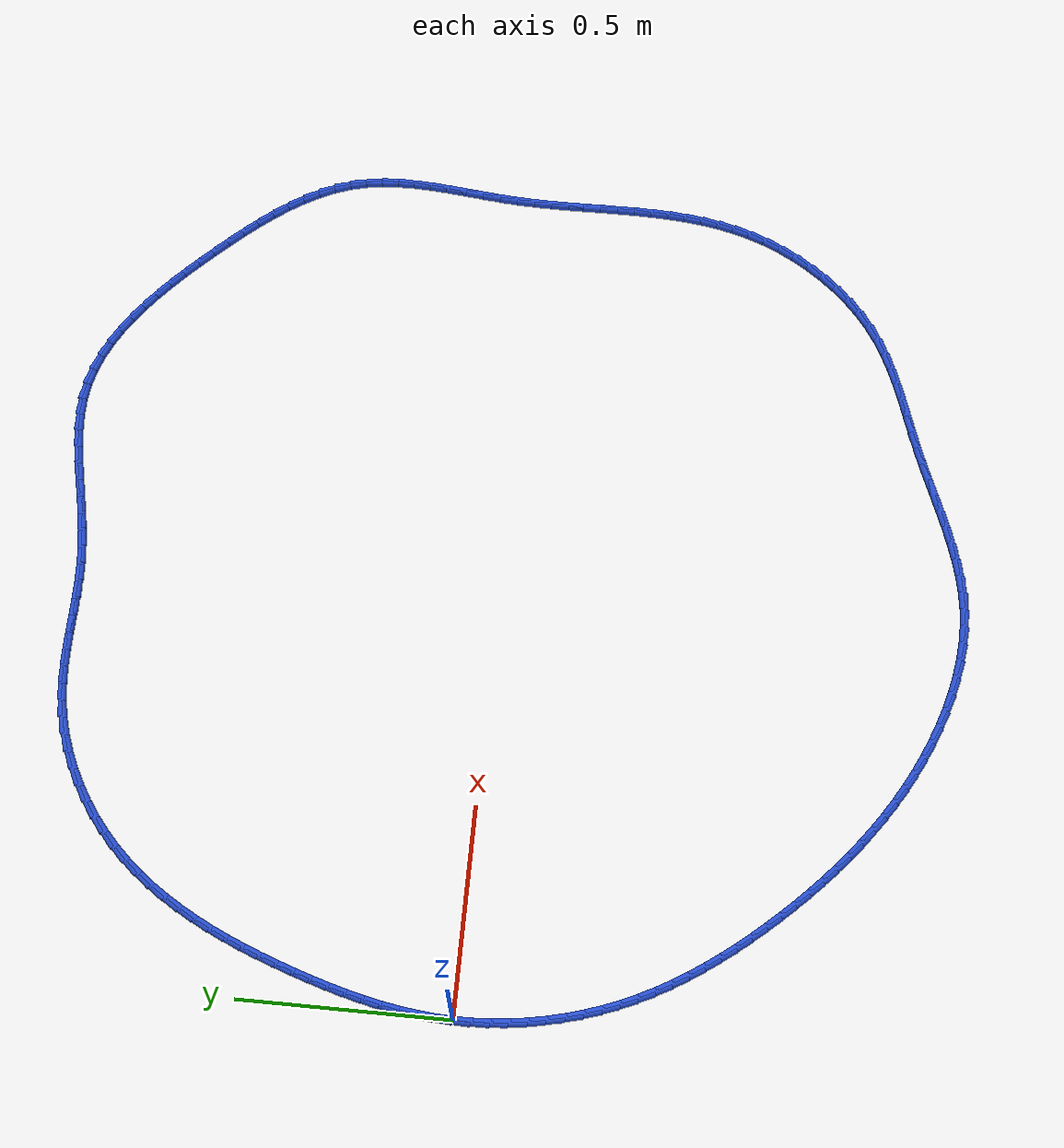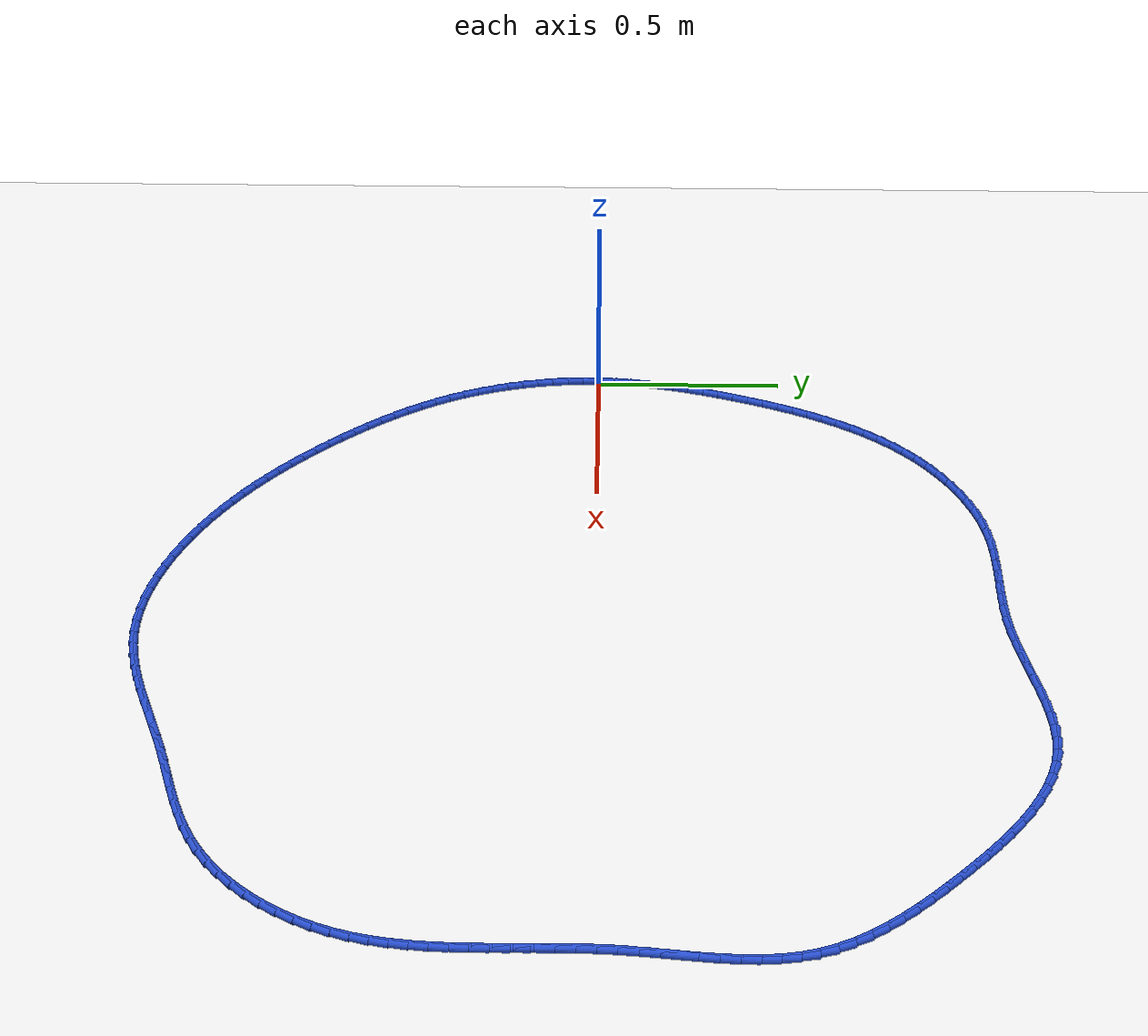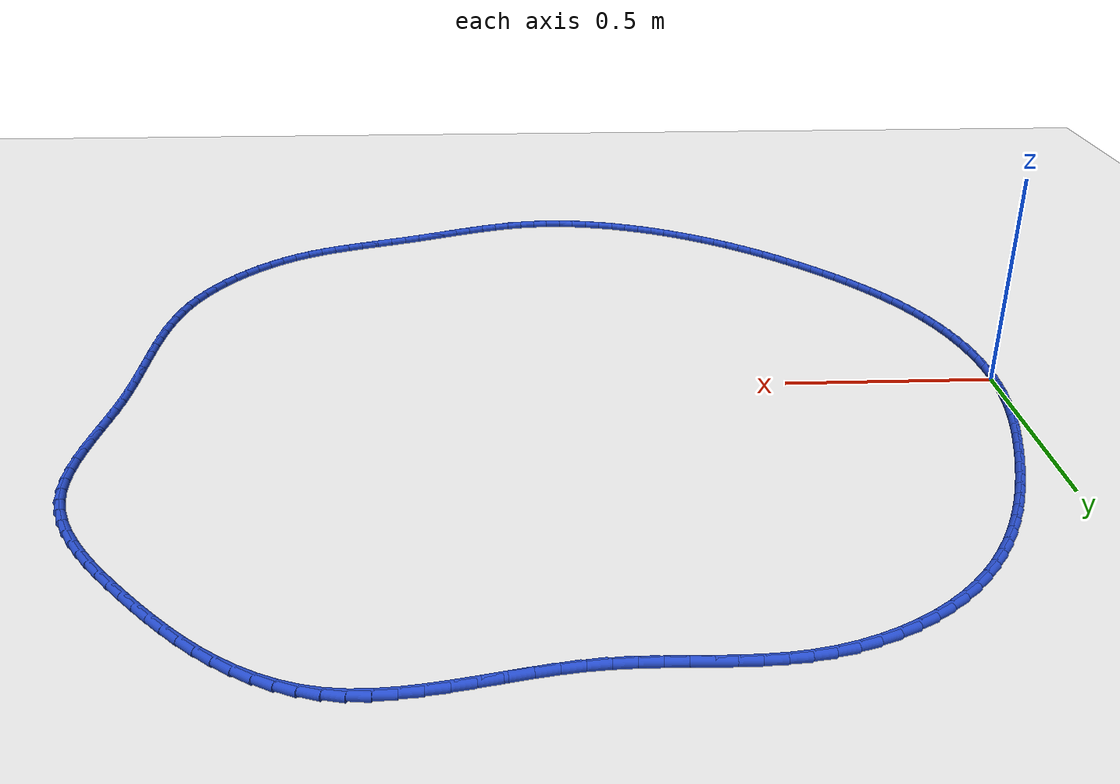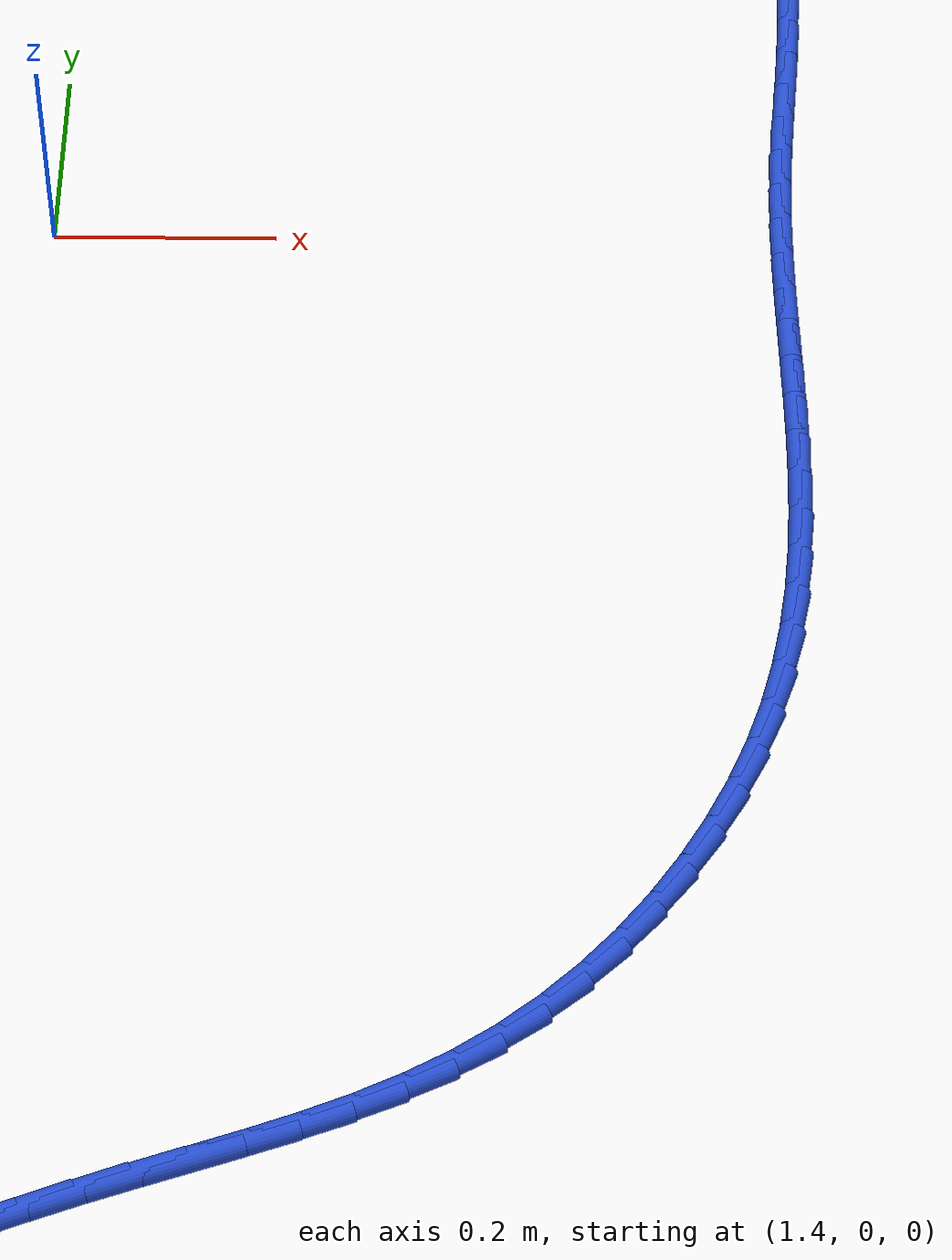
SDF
<sdf version="1.6">
 <world name="default">
  <light name="sun" type="directional">
   <pose>0 0 10 0 -0 0</pose>
   <diffuse>0.8 0.8 0.8 1</diffuse>
   <specular>0.2 0.2 0.2 1</specular>
   <attenuation>
    <range>1000</range>
    <constant>0.9</constant>
    <linear>0.01</linear>
    <quadratic>0.001</quadratic>
   </attenuation>
   <direction>-0.5 0.1 -0.9</direction>
  </light>
  <model name="ground_plane">
   <static>1</static>
   <link name="link">
    <collision name="collision">
     <geometry><plane><normal>0 0 1</normal><size>100 100</size></plane></geometry>
     <surface><friction><ode><mu>100</mu><mu2>50</mu2></ode></friction></surface>
    </collision>
    <visual name="visual">
     <cast_shadows>0</cast_shadows>
     <geometry><plane><normal>0 0 1</normal><size>100 100</size></plane></geometry>
     <material>
      <script><uri>file://media/materials/scripts/gazebo.material</uri><name>Gazebo/WhiteGlow</name></script>
     </material>
    </visual>
   </link>
  </model>
  <gravity>0 0 -9.8</gravity>
  <magnetic_field>6e-06 2.3e-05 -4.2e-05</magnetic_field>
  <atmosphere type="adiabatic"/>
  <physics name="default_physics" default="0" type="ode">
   <max_step_size>0.001</max_step_size>
   <real_time_factor>1</real_time_factor>
   <real_time_update_rate>1000</real_time_update_rate>
  </physics>
  <scene><ambient>0.4 0.4 0.4 1</ambient><background>0.7 0.7 0.7 1</background><shadows>1</shadows></scene>
  <spherical_coordinates>
   <surface_model>EARTH_WGS84</surface_model>
   <latitude_deg>0</latitude_deg>
   <longitude_deg>0</longitude_deg>
   <elevation>0</elevation>
   <heading_deg>0</heading_deg>
  </spherical_coordinates>
  <model name="line">
   <link name="link_0">
    <pose>1.5612511283791264e-17 0.0 0.01 0 1.57 1.5275318421198896</pose>
    <collision name="collision">
     <geometry><cylinder><radius>0.01</radius><length>0.08</length></cylinder></geometry>
    </collision>
    <visual name="visual">
     <material>
      <script><name>Gazebo/Blue</name><uri>file://media/materials/scripts/gazebo.material</uri></script>
     </material>
     <geometry><cylinder><radius>0.01</radius><length>0.08</length></cylinder></geometry>
    </visual>
   </link>
   <link name="link_1">
    <pose>0.0018280608076796574 0.04222678442711341 0.01 0 1.57 1.4818943079029208</pose>
    <collision name="collision">
     <geometry><cylinder><radius>0.01</radius><length>0.08</length></cylinder></geometry>
    </collision>
    <visual name="visual">
     <material>
      <script><name>Gazebo/Blue</name><uri>file://media/materials/scripts/gazebo.material</uri></script>
     </material>
     <geometry><cylinder><radius>0.01</radius><length>0.08</length></cylinder></geometry>
    </visual>
   </link>
   <link name="link_2">
    <pose>0.005574457518726217 0.08425644342598523 0.01 0 1.57 1.4396662999650804</pose>
    <collision name="collision">
     <geometry><cylinder><radius>0.01</radius><length>0.08</length></cylinder></geometry>
    </collision>
    <visual name="visual">
     <material>
      <script><name>Gazebo/Blue</name><uri>file://media/materials/scripts/gazebo.material</uri></script>
     </material>
     <geometry><cylinder><radius>0.01</radius><length>0.08</length></cylinder></geometry>
    </visual>
   </link>
   <link name="link_3">
    <pose>0.011093367865162115 0.12610224677798712 0.01 0 1.57 1.4009882460465606</pose>
    <collision name="collision">
     <geometry><cylinder><radius>0.01</radius><length>0.08</length></cylinder></geometry>
    </collision>
    <visual name="visual">
     <material>
      <script><name>Gazebo/Blue</name><uri>file://media/materials/scripts/gazebo.material</uri></script>
     </material>
     <geometry><cylinder><radius>0.01</radius><length>0.08</length></cylinder></geometry>
    </visual>
   </link>
   <link name="link_4">
    <pose>0.018238969579009702 0.16777746426449028 0.01 0 1.57 1.3659340539052254</pose>
    <collision name="collision">
     <geometry><cylinder><radius>0.01</radius><length>0.08</length></cylinder></geometry>
    </collision>
    <visual name="visual">
     <material>
      <script><name>Gazebo/Blue</name><uri>file://media/materials/scripts/gazebo.material</uri></script>
     </material>
     <geometry><cylinder><radius>0.01</radius><length>0.08</length></cylinder></geometry>
    </visual>
   </link>
   <link name="link_5">
    <pose>0.026865440392291398 0.2092953656668664 0.01 0 1.57 1.3345249050419767</pose>
    <collision name="collision">
     <geometry><cylinder><radius>0.01</radius><length>0.08</length></cylinder></geometry>
    </collision>
    <visual name="visual">
     <material>
      <script><name>Gazebo/Blue</name><uri>file://media/materials/scripts/gazebo.material</uri></script>
     </material>
     <geometry><cylinder><radius>0.01</radius><length>0.08</length></cylinder></geometry>
    </visual>
   </link>
   <link name="link_6">
    <pose>0.03682695803702958 0.25066922076648684 0.01 0 1.57 1.3067430301602199</pose>
    <collision name="collision">
     <geometry><cylinder><radius>0.01</radius><length>0.08</length></cylinder></geometry>
    </collision>
    <visual name="visual">
     <material>
      <script><name>Gazebo/Blue</name><uri>file://media/materials/scripts/gazebo.material</uri></script>
     </material>
     <geometry><cylinder><radius>0.01</radius><length>0.08</length></cylinder></geometry>
    </visual>
   </link>
   <link name="link_7">
    <pose>0.04797770024524663 0.29191229934472296 0.01 0 1.57 1.2825444079119719</pose>
    <collision name="collision">
     <geometry><cylinder><radius>0.01</radius><length>0.08</length></cylinder></geometry>
    </collision>
    <visual name="visual">
     <material>
      <script><name>Gazebo/Blue</name><uri>file://media/materials/scripts/gazebo.material</uri></script>
     </material>
     <geometry><cylinder><radius>0.01</radius><length>0.08</length></cylinder></geometry>
    </visual>
   </link>
   <link name="link_8">
    <pose>0.06017184474896492 0.3330378711829463 0.01 0 1.57 1.261869805388426</pose>
    <collision name="collision">
     <geometry><cylinder><radius>0.01</radius><length>0.08</length></cylinder></geometry>
    </collision>
    <visual name="visual">
     <material>
      <script><name>Gazebo/Blue</name><uri>file://media/materials/scripts/gazebo.material</uri></script>
     </material>
     <geometry><cylinder><radius>0.01</radius><length>0.08</length></cylinder></geometry>
    </visual>
   </link>
   <link name="link_9">
    <pose>0.07326356928020687 0.3740592060625284 0.01 0 1.57 1.244089831451176</pose>
    <collision name="collision">
     <geometry><cylinder><radius>0.01</radius><length>0.08</length></cylinder></geometry>
    </collision>
    <visual name="visual">
     <material>
      <script><name>Gazebo/Blue</name><uri>file://media/materials/scripts/gazebo.material</uri></script>
     </material>
     <geometry><cylinder><radius>0.01</radius><length>0.08</length></cylinder></geometry>
    </visual>
   </link>
   <link name="link_10">
    <pose>0.0871284622791014 0.4149768102350473 0.01 0 1.57 1.2248210727207574</pose>
    <collision name="collision">
     <geometry><cylinder><radius>0.01</radius><length>0.08</length></cylinder></geometry>
    </collision>
    <visual name="visual">
     <material>
      <script><name>Gazebo/Blue</name><uri>file://media/materials/scripts/gazebo.material</uri></script>
     </material>
     <geometry><cylinder><radius>0.01</radius><length>0.08</length></cylinder></geometry>
    </visual>
   </link>
   <link name="link_11">
    <pose>0.10180581301439189 0.4556936032495387 0.01 0 1.57 1.201978175526841</pose>
    <collision name="collision">
     <geometry><cylinder><radius>0.01</radius><length>0.08</length></cylinder></geometry>
    </collision>
    <visual name="visual">
     <material>
      <script><name>Gazebo/Blue</name><uri>file://media/materials/scripts/gazebo.material</uri></script>
     </material>
     <geometry><cylinder><radius>0.01</radius><length>0.08</length></cylinder></geometry>
    </visual>
   </link>
   <link name="link_12">
    <pose>0.11741047524486156 0.49606745852134027 0.01 0 1.57 1.1754284877752654</pose>
    <collision name="collision">
     <geometry><cylinder><radius>0.01</radius><length>0.08</length></cylinder></geometry>
    </collision>
    <visual name="visual">
     <material>
      <script><name>Gazebo/Blue</name><uri>file://media/materials/scripts/gazebo.material</uri></script>
     </material>
     <geometry><cylinder><radius>0.01</radius><length>0.08</length></cylinder></geometry>
    </visual>
   </link>
   <link name="link_13">
    <pose>0.13405770877414447 0.5359560074109481 0.01 0 1.57 1.1450301556905935</pose>
    <collision name="collision">
     <geometry><cylinder><radius>0.01</radius><length>0.08</length></cylinder></geometry>
    </collision>
    <visual name="visual">
     <material>
      <script><name>Gazebo/Blue</name><uri>file://media/materials/scripts/gazebo.material</uri></script>
     </material>
     <geometry><cylinder><radius>0.01</radius><length>0.08</length></cylinder></geometry>
    </visual>
   </link>
   <link name="link_14">
    <pose>0.15186277340587476 0.5752168812788586 0.01 0 1.57 1.1106311081727345</pose>
    <collision name="collision">
     <geometry><cylinder><radius>0.01</radius><length>0.08</length></cylinder></geometry>
    </collision>
    <visual name="visual">
     <material>
      <script><name>Gazebo/Blue</name><uri>file://media/materials/scripts/gazebo.material</uri></script>
     </material>
     <geometry><cylinder><radius>0.01</radius><length>0.08</length></cylinder></geometry>
    </visual>
   </link>
   <link name="link_15">
    <pose>0.1709409289436863 0.6137077114855682 0.01 0 1.57 1.072081762744674</pose>
    <collision name="collision">
     <geometry><cylinder><radius>0.01</radius><length>0.08</length></cylinder></geometry>
    </collision>
    <visual name="visual">
     <material>
      <script><name>Gazebo/Blue</name><uri>file://media/materials/scripts/gazebo.material</uri></script>
     </material>
     <geometry><cylinder><radius>0.01</radius><length>0.08</length></cylinder></geometry>
    </visual>
   </link>
   <link name="link_16">
    <pose>0.19140743519121328 0.6512861293915729 0.01 0 1.57 1.0292515119248666</pose>
    <collision name="collision">
     <geometry><cylinder><radius>0.01</radius><length>0.08</length></cylinder></geometry>
    </collision>
    <visual name="visual">
     <material>
      <script><name>Gazebo/Blue</name><uri>file://media/materials/scripts/gazebo.material</uri></script>
     </material>
     <geometry><cylinder><radius>0.01</radius><length>0.08</length></cylinder></geometry>
    </visual>
   </link>
   <link name="link_17">
    <pose>0.2133775519520898 0.6878097663573695 0.01 0 1.57 0.9820494796564899</pose>
    <collision name="collision">
     <geometry><cylinder><radius>0.01</radius><length>0.08</length></cylinder></geometry>
    </collision>
    <visual name="visual">
     <material>
      <script><name>Gazebo/Blue</name><uri>file://media/materials/scripts/gazebo.material</uri></script>
     </material>
     <geometry><cylinder><radius>0.01</radius><length>0.08</length></cylinder></geometry>
    </visual>
   </link>
   <link name="link_18">
    <pose>0.23696653902994977 0.7231362537434536 0.01 0 1.57 0.9304494518284931</pose>
    <collision name="collision">
     <geometry><cylinder><radius>0.01</radius><length>0.08</length></cylinder></geometry>
    </collision>
    <visual name="visual">
     <material>
      <script><name>Gazebo/Blue</name><uri>file://media/materials/scripts/gazebo.material</uri></script>
     </material>
     <geometry><cylinder><radius>0.01</radius><length>0.08</length></cylinder></geometry>
    </visual>
   </link>
   <link name="link_19">
    <pose>0.2622896562284273 0.7571232229103221 0.01 0 1.57 0.8745178827878001</pose>
    <collision name="collision">
     <geometry><cylinder><radius>0.01</radius><length>0.08</length></cylinder></geometry>
    </collision>
    <visual name="visual">
     <material>
      <script><name>Gazebo/Blue</name><uri>file://media/materials/scripts/gazebo.material</uri></script>
     </material>
     <geometry><cylinder><radius>0.01</radius><length>0.08</length></cylinder></geometry>
    </visual>
   </link>
   <link name="link_20">
    <pose>0.2894621633511564 0.7896283052184709 0.01 0 1.57 0.8144424518333424</pose>
    <collision name="collision">
     <geometry><cylinder><radius>0.01</radius><length>0.08</length></cylinder></geometry>
    </collision>
    <visual name="visual">
     <material>
      <script><name>Gazebo/Blue</name><uri>file://media/materials/scripts/gazebo.material</uri></script>
     </material>
     <geometry><cylinder><radius>0.01</radius><length>0.08</length></cylinder></geometry>
    </visual>
   </link>
   <link name="link_21">
    <pose>0.3185993202017712 0.8205091320283965 0.01 0 1.57 0.7505854759910814</pose>
    <collision name="collision">
     <geometry><cylinder><radius>0.01</radius><length>0.08</length></cylinder></geometry>
    </collision>
    <visual name="visual">
     <material>
      <script><name>Gazebo/Blue</name><uri>file://media/materials/scripts/gazebo.material</uri></script>
     </material>
     <geometry><cylinder><radius>0.01</radius><length>0.08</length></cylinder></geometry>
    </visual>
   </link>
   <link name="link_22">
    <pose>0.3498143501638152 0.8496230986465624 0.01 0 1.57 0.6850379300311572</pose>
    <collision name="collision">
     <geometry><cylinder><radius>0.01</radius><length>0.08</length></cylinder></geometry>
    </collision>
    <visual name="visual">
     <material>
      <script><name>Gazebo/Blue</name><uri>file://media/materials/scripts/gazebo.material</uri></script>
     </material>
     <geometry><cylinder><radius>0.01</radius><length>0.08</length></cylinder></geometry>
    </visual>
   </link>
   <link name="link_23">
    <pose>0.3830931978431265 0.8768128467100171 0.01 0 1.57 0.6201228792375129</pose>
    <collision name="collision">
     <geometry><cylinder><radius>0.01</radius><length>0.08</length></cylinder></geometry>
    </collision>
    <visual name="visual">
     <material>
      <script><name>Gazebo/Blue</name><uri>file://media/materials/scripts/gazebo.material</uri></script>
     </material>
     <geometry><cylinder><radius>0.01</radius><length>0.08</length></cylinder></geometry>
    </visual>
   </link>
   <link name="link_24">
    <pose>0.4182215398264966 0.9018978035525261 0.01 0 1.57 0.5552920562096993</pose>
    <collision name="collision">
     <geometry><cylinder><radius>0.01</radius><length>0.08</length></cylinder></geometry>
    </collision>
    <visual name="visual">
     <material>
      <script><name>Gazebo/Blue</name><uri>file://media/materials/scripts/gazebo.material</uri></script>
     </material>
     <geometry><cylinder><radius>0.01</radius><length>0.08</length></cylinder></geometry>
    </visual>
   </link>
   <link name="link_25">
    <pose>0.454967471570498 0.9246953585704404 0.01 0 1.57 0.48976702150082624</pose>
    <collision name="collision">
     <geometry><cylinder><radius>0.01</radius><length>0.08</length></cylinder></geometry>
    </collision>
    <visual name="visual">
     <material>
      <script><name>Gazebo/Blue</name><uri>file://media/materials/scripts/gazebo.material</uri></script>
     </material>
     <geometry><cylinder><radius>0.01</radius><length>0.08</length></cylinder></geometry>
    </visual>
   </link>
   <link name="link_26">
    <pose>0.4930990885317031 0.9450229011601099 0.01 0 1.57 0.42277963646379285</pose>
    <collision name="collision">
     <geometry><cylinder><radius>0.01</radius><length>0.08</length></cylinder></geometry>
    </collision>
    <visual name="visual">
     <material>
      <script><name>Gazebo/Blue</name><uri>file://media/materials/scripts/gazebo.material</uri></script>
     </material>
     <geometry><cylinder><radius>0.01</radius><length>0.08</length></cylinder></geometry>
    </visual>
   </link>
   <link name="link_27">
    <pose>0.5323844861666845 0.9626978207178857 0.01 0 1.57 0.3535701375745545</pose>
    <collision name="collision">
     <geometry><cylinder><radius>0.01</radius><length>0.08</length></cylinder></geometry>
    </collision>
    <visual name="visual">
     <material>
      <script><name>Gazebo/Blue</name><uri>file://media/materials/scripts/gazebo.material</uri></script>
     </material>
     <geometry><cylinder><radius>0.01</radius><length>0.08</length></cylinder></geometry>
    </visual>
   </link>
   <link name="link_28">
    <pose>0.5725917599320147 0.9775375066401182 0.01 0 1.57 0.2813920196557617</pose>
    <collision name="collision">
     <geometry><cylinder><radius>0.01</radius><length>0.08</length></cylinder></geometry>
    </collision>
    <visual name="visual">
     <material>
      <script><name>Gazebo/Blue</name><uri>file://media/materials/scripts/gazebo.material</uri></script>
     </material>
     <geometry><cylinder><radius>0.01</radius><length>0.08</length></cylinder></geometry>
    </visual>
   </link>
   <link name="link_29">
    <pose>0.6134890052842659 0.989359348323158 0.01 0 1.57 0.2055275365935062</pose>
    <collision name="collision">
     <geometry><cylinder><radius>0.01</radius><length>0.08</length></cylinder></geometry>
    </collision>
    <visual name="visual">
     <material>
      <script><name>Gazebo/Blue</name><uri>file://media/materials/scripts/gazebo.material</uri></script>
     </material>
     <geometry><cylinder><radius>0.01</radius><length>0.08</length></cylinder></geometry>
    </visual>
   </link>
   <link name="link_30">
    <pose>0.6548443191412737 0.9979807410604804 0.01 0 1.57 0.12904279395965584</pose>
    <collision name="collision">
     <geometry><cylinder><radius>0.01</radius><length>0.08</length></cylinder></geometry>
    </collision>
    <visual name="visual">
     <material>
      <script><name>Gazebo/Blue</name><uri>file://media/materials/scripts/gazebo.material</uri></script>
     </material>
     <geometry><cylinder><radius>0.01</radius><length>0.08</length></cylinder></geometry>
    </visual>
   </link>
   <link name="link_31">
    <pose>0.6964661056174482 1.0033817452616896 0.01 0 1.57 0.06557926179460562</pose>
    <collision name="collision">
     <geometry><cylinder><radius>0.01</radius><length>0.08</length></cylinder></geometry>
    </collision>
    <visual name="visual">
     <material>
      <script><name>Gazebo/Blue</name><uri>file://media/materials/scripts/gazebo.material</uri></script>
     </material>
     <geometry><cylinder><radius>0.01</radius><length>0.08</length></cylinder></geometry>
    </visual>
   </link>
   <link name="link_32">
    <pose>0.7383082833534815 1.0061296647898785 0.01 0 1.57 0.01889493254458288</pose>
    <collision name="collision">
     <geometry><cylinder><radius>0.01</radius><length>0.08</length></cylinder></geometry>
    </collision>
    <visual name="visual">
     <material>
      <script><name>Gazebo/Blue</name><uri>file://media/materials/scripts/gazebo.material</uri></script>
     </material>
     <geometry><cylinder><radius>0.01</radius><length>0.08</length></cylinder></geometry>
    </visual>
   </link>
   <link name="link_33">
    <pose>0.7803575972519782 1.0069242783056895 0.01 0 1.57 -0.010863188359964675</pose>
    <collision name="collision">
     <geometry><cylinder><radius>0.01</radius><length>0.08</length></cylinder></geometry>
    </collision>
    <visual name="visual">
     <material>
      <script><name>Gazebo/Blue</name><uri>file://media/materials/scripts/gazebo.material</uri></script>
     </material>
     <geometry><cylinder><radius>0.01</radius><length>0.08</length></cylinder></geometry>
    </visual>
   </link>
   <link name="link_34">
    <pose>0.8226007922155418 1.0064653644697652 0.01 0 1.57 -0.023865607521854907</pose>
    <collision name="collision">
     <geometry><cylinder><radius>0.01</radius><length>0.08</length></cylinder></geometry>
    </collision>
    <visual name="visual">
     <material>
      <script><name>Gazebo/Blue</name><uri>file://media/materials/scripts/gazebo.material</uri></script>
     </material>
     <geometry><cylinder><radius>0.01</radius><length>0.08</length></cylinder></geometry>
    </visual>
   </link>
   <link name="link_35">
    <pose>0.8650246131467764 1.005452701942748 0.01 0 1.57 -0.020344886981176764</pose>
    <collision name="collision">
     <geometry><cylinder><radius>0.01</radius><length>0.08</length></cylinder></geometry>
    </collision>
    <visual name="visual">
     <material>
      <script><name>Gazebo/Blue</name><uri>file://media/materials/scripts/gazebo.material</uri></script>
     </material>
     <geometry><cylinder><radius>0.01</radius><length>0.08</length></cylinder></geometry>
    </visual>
   </link>
   <link name="link_36">
    <pose>0.9076158049482866 1.0045860693852804 0.01 0 1.57 -0.0004871628445204199</pose>
    <collision name="collision">
     <geometry><cylinder><radius>0.01</radius><length>0.08</length></cylinder></geometry>
    </collision>
    <visual name="visual">
     <material>
      <script><name>Gazebo/Blue</name><uri>file://media/materials/scripts/gazebo.material</uri></script>
     </material>
     <geometry><cylinder><radius>0.01</radius><length>0.08</length></cylinder></geometry>
    </visual>
   </link>
   <link name="link_37">
    <pose>0.9503611125226759 1.0045652454580052 0.01 0 1.57 0.03553876329933855</pose>
    <collision name="collision">
     <geometry><cylinder><radius>0.01</radius><length>0.08</length></cylinder></geometry>
    </collision>
    <visual name="visual">
     <material>
      <script><name>Gazebo/Blue</name><uri>file://media/materials/scripts/gazebo.material</uri></script>
     </material>
     <geometry><cylinder><radius>0.01</radius><length>0.08</length></cylinder></geometry>
    </visual>
   </link>
   <link name="link_38">
    <pose>0.9932472807725489 1.006090008821565 0.01 0 1.57 0.08709508095258915</pose>
    <collision name="collision">
     <geometry><cylinder><radius>0.01</radius><length>0.08</length></cylinder></geometry>
    </collision>
    <visual name="visual">
     <material>
      <script><name>Gazebo/Blue</name><uri>file://media/materials/scripts/gazebo.material</uri></script>
     </material>
     <geometry><cylinder><radius>0.01</radius><length>0.08</length></cylinder></geometry>
    </visual>
   </link>
   <link name="link_39">
    <pose>1.0362602418158438 1.0098457273522907 0.01 0 1.57 0.14040850093729512</pose>
    <collision name="collision">
     <geometry><cylinder><radius>0.01</radius><length>0.08</length></cylinder></geometry>
    </collision>
    <visual name="visual">
     <material>
      <script><name>Gazebo/Blue</name><uri>file://media/materials/scripts/gazebo.material</uri></script>
     </material>
     <geometry><cylinder><radius>0.01</radius><length>0.08</length></cylinder></geometry>
    </visual>
   </link>
   <link name="link_40">
    <pose>1.0793531386984072 1.0159364141526273 0.01 0 1.57 0.17825313718337404</pose>
    <collision name="collision">
     <geometry><cylinder><radius>0.01</radius><length>0.08</length></cylinder></geometry>
    </collision>
    <visual name="visual">
     <material>
      <script><name>Gazebo/Blue</name><uri>file://media/materials/scripts/gazebo.material</uri></script>
     </material>
     <geometry><cylinder><radius>0.01</radius><length>0.08</length></cylinder></geometry>
    </visual>
   </link>
   <link name="link_41">
    <pose>1.1224358175467575 1.0236984219691931 0.01 0 1.57 0.20010639664537083</pose>
    <collision name="collision">
     <geometry><cylinder><radius>0.01</radius><length>0.08</length></cylinder></geometry>
    </collision>
    <visual name="visual">
     <material>
      <script><name>Gazebo/Blue</name><uri>file://media/materials/scripts/gazebo.material</uri></script>
     </material>
     <geometry><cylinder><radius>0.01</radius><length>0.08</length></cylinder></geometry>
    </visual>
   </link>
   <link name="link_42">
    <pose>1.16541515909238 1.0324155266854427 0.01 0 1.57 0.20635569568912285</pose>
    <collision name="collision">
     <geometry><cylinder><radius>0.01</radius><length>0.08</length></cylinder></geometry>
    </collision>
    <visual name="visual">
     <material>
      <script><name>Gazebo/Blue</name><uri>file://media/materials/scripts/gazebo.material</uri></script>
     </material>
     <geometry><cylinder><radius>0.01</radius><length>0.08</length></cylinder></geometry>
    </visual>
   </link>
   <link name="link_43">
    <pose>1.2081980440667628 1.0413715041848297 0.01 0 1.57 0.19694215189788464</pose>
    <collision name="collision">
     <geometry><cylinder><radius>0.01</radius><length>0.08</length></cylinder></geometry>
    </collision>
    <visual name="visual">
     <material>
      <script><name>Gazebo/Blue</name><uri>file://media/materials/scripts/gazebo.material</uri></script>
     </material>
     <geometry><cylinder><radius>0.01</radius><length>0.08</length></cylinder></geometry>
    </visual>
   </link>
   <link name="link_44">
    <pose>1.2506913532013932 1.0498501303508094 0.01 0 1.57 0.17130246799780782</pose>
    <collision name="collision">
     <geometry><cylinder><radius>0.01</radius><length>0.08</length></cylinder></geometry>
    </collision>
    <visual name="visual">
     <material>
      <script><name>Gazebo/Blue</name><uri>file://media/materials/scripts/gazebo.material</uri></script>
     </material>
     <geometry><cylinder><radius>0.01</radius><length>0.08</length></cylinder></geometry>
    </visual>
   </link>
   <link name="link_45">
    <pose>1.2928019672277582 1.057135181066836 0.01 0 1.57 0.12839454949498158</pose>
    <collision name="collision">
     <geometry><cylinder><radius>0.01</radius><length>0.08</length></cylinder></geometry>
    </collision>
    <visual name="visual">
     <material>
      <script><name>Gazebo/Blue</name><uri>file://media/materials/scripts/gazebo.material</uri></script>
     </material>
     <geometry><cylinder><radius>0.01</radius><length>0.08</length></cylinder></geometry>
    </visual>
   </link>
   <link name="link_46">
    <pose>1.3344367668773451 1.062510432216364 0.01 0 1.57 0.06684703174045518</pose>
    <collision name="collision">
     <geometry><cylinder><radius>0.01</radius><length>0.08</length></cylinder></geometry>
    </collision>
    <visual name="visual">
     <material>
      <script><name>Gazebo/Blue</name><uri>file://media/materials/scripts/gazebo.material</uri></script>
     </material>
     <geometry><cylinder><radius>0.01</radius><length>0.08</length></cylinder></geometry>
    </visual>
   </link>
   <link name="link_47">
    <pose>1.3755026328816409 1.0652596596828483 0.01 0 1.57 -0.014676282004360705</pose>
    <collision name="collision">
     <geometry><cylinder><radius>0.01</radius><length>0.08</length></cylinder></geometry>
    </collision>
    <visual name="visual">
     <material>
      <script><name>Gazebo/Blue</name><uri>file://media/materials/scripts/gazebo.material</uri></script>
     </material>
     <geometry><cylinder><radius>0.01</radius><length>0.08</length></cylinder></geometry>
    </visual>
   </link>
   <link name="link_48">
    <pose>1.4159064459721336 1.064666639349743 0.01 0 1.57 -0.11672054544691289</pose>
    <collision name="collision">
     <geometry><cylinder><radius>0.01</radius><length>0.08</length></cylinder></geometry>
    </collision>
    <visual name="visual">
     <material>
      <script><name>Gazebo/Blue</name><uri>file://media/materials/scripts/gazebo.material</uri></script>
     </material>
     <geometry><cylinder><radius>0.01</radius><length>0.08</length></cylinder></geometry>
    </visual>
   </link>
   <link name="link_49">
    <pose>1.4555553449067007 1.060017666993778 0.01 0 1.57 -0.2296459802357283</pose>
    <collision name="collision">
     <geometry><cylinder><radius>0.01</radius><length>0.08</length></cylinder></geometry>
    </collision>
    <visual name="visual">
     <material>
      <script><name>Gazebo/Blue</name><uri>file://media/materials/scripts/gazebo.material</uri></script>
     </material>
     <geometry><cylinder><radius>0.01</radius><length>0.08</length></cylinder></geometry>
    </visual>
   </link>
   <link name="link_50">
    <pose>1.4943912782731497 1.0509389922077446 0.01 0 1.57 -0.3340972530840046</pose>
    <collision name="collision">
     <geometry><cylinder><radius>0.01</radius><length>0.08</length></cylinder></geometry>
    </collision>
    <visual name="visual">
     <material>
      <script><name>Gazebo/Blue</name><uri>file://media/materials/scripts/gazebo.material</uri></script>
     </material>
     <geometry><cylinder><radius>0.01</radius><length>0.08</length></cylinder></geometry>
    </visual>
   </link>
   <link name="link_51">
    <pose>1.5324258221747142 1.0377368489342567 0.01 0 1.57 -0.42674391120072797</pose>
    <collision name="collision">
     <geometry><cylinder><radius>0.01</radius><length>0.08</length></cylinder></geometry>
    </collision>
    <visual name="visual">
     <material>
      <script><name>Gazebo/Blue</name><uri>file://media/materials/scripts/gazebo.material</uri></script>
     </material>
     <geometry><cylinder><radius>0.01</radius><length>0.08</length></cylinder></geometry>
    </visual>
   </link>
   <link name="link_52">
    <pose>1.5696788420317873 1.0207984248295154 0.01 0 1.57 -0.507402904426464</pose>
    <collision name="collision">
     <geometry><cylinder><radius>0.01</radius><length>0.08</length></cylinder></geometry>
    </collision>
    <visual name="visual">
     <material>
      <script><name>Gazebo/Blue</name><uri>file://media/materials/scripts/gazebo.material</uri></script>
     </material>
     <geometry><cylinder><radius>0.01</radius><length>0.08</length></cylinder></geometry>
    </visual>
   </link>
   <link name="link_53">
    <pose>1.606170203264766 1.0005109075497223 0.01 0 1.57 -0.5766151571464926</pose>
    <collision name="collision">
     <geometry><cylinder><radius>0.01</radius><length>0.08</length></cylinder></geometry>
    </collision>
    <visual name="visual">
     <material>
      <script><name>Gazebo/Blue</name><uri>file://media/materials/scripts/gazebo.material</uri></script>
     </material>
     <geometry><cylinder><radius>0.01</radius><length>0.08</length></cylinder></geometry>
    </visual>
   </link>
   <link name="link_54">
    <pose>1.641919771294044 0.9772614847510781 0.01 0 1.57 -0.635291284964375</pose>
    <collision name="collision">
     <geometry><cylinder><radius>0.01</radius><length>0.08</length></cylinder></geometry>
    </collision>
    <visual name="visual">
     <material>
      <script><name>Gazebo/Blue</name><uri>file://media/materials/scripts/gazebo.material</uri></script>
     </material>
     <geometry><cylinder><radius>0.01</radius><length>0.08</length></cylinder></geometry>
    </visual>
   </link>
   <link name="link_55">
    <pose>1.6769474115400178 0.9514373440897841 0.01 0 1.57 -0.684456145345269</pose>
    <collision name="collision">
     <geometry><cylinder><radius>0.01</radius><length>0.08</length></cylinder></geometry>
    </collision>
    <visual name="visual">
     <material>
      <script><name>Gazebo/Blue</name><uri>file://media/materials/scripts/gazebo.material</uri></script>
     </material>
     <geometry><cylinder><radius>0.01</radius><length>0.08</length></cylinder></geometry>
    </visual>
   </link>
   <link name="link_56">
    <pose>1.711272989423082 0.9234256732220407 0.01 0 1.57 -0.7250924663818041</pose>
    <collision name="collision">
     <geometry><cylinder><radius>0.01</radius><length>0.08</length></cylinder></geometry>
    </collision>
    <visual name="visual">
     <material>
      <script><name>Gazebo/Blue</name><uri>file://media/materials/scripts/gazebo.material</uri></script>
     </material>
     <geometry><cylinder><radius>0.01</radius><length>0.08</length></cylinder></geometry>
    </visual>
   </link>
   <link name="link_57">
    <pose>1.7449163703636315 0.8936136598040496 0.01 0 1.57 -0.75805745355408</pose>
    <collision name="collision">
     <geometry><cylinder><radius>0.01</radius><length>0.08</length></cylinder></geometry>
    </collision>
    <visual name="visual">
     <material>
      <script><name>Gazebo/Blue</name><uri>file://media/materials/scripts/gazebo.material</uri></script>
     </material>
     <geometry><cylinder><radius>0.01</radius><length>0.08</length></cylinder></geometry>
    </visual>
   </link>
   <link name="link_58">
    <pose>1.7778974197820625 0.8623884914920115 0.01 0 1.57 -0.7840442681502652</pose>
    <collision name="collision">
     <geometry><cylinder><radius>0.01</radius><length>0.08</length></cylinder></geometry>
    </collision>
    <visual name="visual">
     <material>
      <script><name>Gazebo/Blue</name><uri>file://media/materials/scripts/gazebo.material</uri></script>
     </material>
     <geometry><cylinder><radius>0.01</radius><length>0.08</length></cylinder></geometry>
    </visual>
   </link>
   <link name="link_59">
    <pose>1.8102360030987683 0.8301373559421276 0.01 0 1.57 -0.803566834709716</pose>
    <collision name="collision">
     <geometry><cylinder><radius>0.01</radius><length>0.08</length></cylinder></geometry>
    </collision>
    <visual name="visual">
     <material>
      <script><name>Gazebo/Blue</name><uri>file://media/materials/scripts/gazebo.material</uri></script>
     </material>
     <geometry><cylinder><radius>0.01</radius><length>0.08</length></cylinder></geometry>
    </visual>
   </link>
   <link name="link_60">
    <pose>1.8419519857341462 0.7972474408105988 0.01 0 1.57 -0.8186216417248469</pose>
    <collision name="collision">
     <geometry><cylinder><radius>0.01</radius><length>0.08</length></cylinder></geometry>
    </collision>
    <visual name="visual">
     <material>
      <script><name>Gazebo/Blue</name><uri>file://media/materials/scripts/gazebo.material</uri></script>
     </material>
     <geometry><cylinder><radius>0.01</radius><length>0.08</length></cylinder></geometry>
    </visual>
   </link>
   <link name="link_61">
    <pose>1.8730176154194262 0.7640458443804568 0.01 0 1.57 -0.8381725714186723</pose>
    <collision name="collision">
     <geometry><cylinder><radius>0.01</radius><length>0.08</length></cylinder></geometry>
    </collision>
    <visual name="visual">
     <material>
      <script><name>Gazebo/Blue</name><uri>file://media/materials/scripts/gazebo.material</uri></script>
     </material>
     <geometry><cylinder><radius>0.01</radius><length>0.08</length></cylinder></geometry>
    </visual>
   </link>
   <link name="link_62">
    <pose>1.9031562481956132 0.7305455853161041 0.01 0 1.57 -0.8654636048547081</pose>
    <collision name="collision">
     <geometry><cylinder><radius>0.01</radius><length>0.08</length></cylinder></geometry>
    </collision>
    <visual name="visual">
     <material>
      <script><name>Gazebo/Blue</name><uri>file://media/materials/scripts/gazebo.material</uri></script>
     </material>
     <geometry><cylinder><radius>0.01</radius><length>0.08</length></cylinder></geometry>
    </visual>
   </link>
   <link name="link_63">
    <pose>1.9320101907741576 0.6966574050926418 0.01 0 1.57 -0.9010579109764761</pose>
    <collision name="collision">
     <geometry><cylinder><radius>0.01</radius><length>0.08</length></cylinder></geometry>
    </collision>
    <visual name="visual">
     <material>
      <script><name>Gazebo/Blue</name><uri>file://media/materials/scripts/gazebo.material</uri></script>
     </material>
     <geometry><cylinder><radius>0.01</radius><length>0.08</length></cylinder></geometry>
    </visual>
   </link>
   <link name="link_64">
    <pose>1.9592217058436445 0.662291989632152 0.01 0 1.57 -0.9456366709047839</pose>
    <collision name="collision">
     <geometry><cylinder><radius>0.01</radius><length>0.08</length></cylinder></geometry>
    </collision>
    <visual name="visual">
     <material>
      <script><name>Gazebo/Blue</name><uri>file://media/materials/scripts/gazebo.material</uri></script>
     </material>
     <geometry><cylinder><radius>0.01</radius><length>0.08</length></cylinder></geometry>
    </visual>
   </link>
   <link name="link_65">
    <pose>1.984433056092657 0.6273600248567145 0.01 0 1.57 -0.9999449595936909</pose>
    <collision name="collision">
     <geometry><cylinder><radius>0.01</radius><length>0.08</length></cylinder></geometry>
    </collision>
    <visual name="visual">
     <material>
      <script><name>Gazebo/Blue</name><uri>file://media/materials/scripts/gazebo.material</uri></script>
     </material>
     <geometry><cylinder><radius>0.01</radius><length>0.08</length></cylinder></geometry>
    </visual>
   </link>
   <link name="link_66">
    <pose>2.007286504209779 0.5917721966884102 0.01 0 1.57 -1.0646909573145942</pose>
    <collision name="collision">
     <geometry><cylinder><radius>0.01</radius><length>0.08</length></cylinder></geometry>
    </collision>
    <visual name="visual">
     <material>
      <script><name>Gazebo/Blue</name><uri>file://media/materials/scripts/gazebo.material</uri></script>
     </material>
     <geometry><cylinder><radius>0.01</radius><length>0.08</length></cylinder></geometry>
    </visual>
   </link>
   <link name="link_67">
    <pose>2.0274243128835945 0.5554391910493204 0.01 0 1.57 -1.1403821275413921</pose>
    <collision name="collision">
     <geometry><cylinder><radius>0.01</radius><length>0.08</length></cylinder></geometry>
    </collision>
    <visual name="visual">
     <material>
      <script><name>Gazebo/Blue</name><uri>file://media/materials/scripts/gazebo.material</uri></script>
     </material>
     <geometry><cylinder><radius>0.01</radius><length>0.08</length></cylinder></geometry>
    </visual>
   </link>
   <link name="link_68">
    <pose>2.0444887448026865 0.5182716938615252 0.01 0 1.57 -1.2270908013206259</pose>
    <collision name="collision">
     <geometry><cylinder><radius>0.01</radius><length>0.08</length></cylinder></geometry>
    </collision>
    <visual name="visual">
     <material>
      <script><name>Gazebo/Blue</name><uri>file://media/materials/scripts/gazebo.material</uri></script>
     </material>
     <geometry><cylinder><radius>0.01</radius><length>0.08</length></cylinder></geometry>
    </visual>
   </link>
   <link name="link_69">
    <pose>2.0581220626556394 0.480180391047106 0.01 0 1.57 -1.3238222673509852</pose>
    <collision name="collision">
     <geometry><cylinder><radius>0.01</radius><length>0.08</length></cylinder></geometry>
    </collision>
    <visual name="visual">
     <material>
      <script><name>Gazebo/Blue</name><uri>file://media/materials/scripts/gazebo.material</uri></script>
     </material>
     <geometry><cylinder><radius>0.01</radius><length>0.08</length></cylinder></geometry>
    </visual>
   </link>
   <link name="link_70">
    <pose>2.0679803225079194 0.441079113395375 0.01 0 1.57 -1.4185675452661772</pose>
    <collision name="collision">
     <geometry><cylinder><radius>0.01</radius><length>0.08</length></cylinder></geometry>
    </collision>
    <visual name="visual">
     <material>
      <script><name>Gazebo/Blue</name><uri>file://media/materials/scripts/gazebo.material</uri></script>
     </material>
     <geometry><cylinder><radius>0.01</radius><length>0.08</length></cylinder></geometry>
    </visual>
   </link>
   <link name="link_71">
    <pose>2.074132784080292 0.40097590144910705 0.01 0 1.57 -1.4979611683045215</pose>
    <collision name="collision">
     <geometry><cylinder><radius>0.01</radius><length>0.08</length></cylinder></geometry>
    </collision>
    <visual name="visual">
     <material>
      <script><name>Gazebo/Blue</name><uri>file://media/materials/scripts/gazebo.material</uri></script>
     </material>
     <geometry><cylinder><radius>0.01</radius><length>0.08</length></cylinder></geometry>
    </visual>
   </link>
   <link name="link_72">
    <pose>2.07712350408935 0.35998704868482706 0.01 0 1.57 -1.5612349297874002</pose>
    <collision name="collision">
     <geometry><cylinder><radius>0.01</radius><length>0.08</length></cylinder></geometry>
    </collision>
    <visual name="visual">
     <material>
      <script><name>Gazebo/Blue</name><uri>file://media/materials/scripts/gazebo.material</uri></script>
     </material>
     <geometry><cylinder><radius>0.01</radius><length>0.08</length></cylinder></geometry>
    </visual>
   </link>
   <link name="link_73">
    <pose>2.0775227258981763 0.31823481909136697 0.01 0 1.57 1.5325534775962923</pose>
    <collision name="collision">
     <geometry><cylinder><radius>0.01</radius><length>0.08</length></cylinder></geometry>
    </collision>
    <visual name="visual">
     <material>
      <script><name>Gazebo/Blue</name><uri>file://media/materials/scripts/gazebo.material</uri></script>
     </material>
     <geometry><cylinder><radius>0.01</radius><length>0.08</length></cylinder></geometry>
    </visual>
   </link>
   <link name="link_74">
    <pose>2.075900692869856 0.2758414766575605 0.01 0 1.57 1.4993059806733562</pose>
    <collision name="collision">
     <geometry><cylinder><radius>0.01</radius><length>0.08</length></cylinder></geometry>
    </collision>
    <visual name="visual">
     <material>
      <script><name>Gazebo/Blue</name><uri>file://media/materials/scripts/gazebo.material</uri></script>
     </material>
     <geometry><cylinder><radius>0.01</radius><length>0.08</length></cylinder></geometry>
    </visual>
   </link>
   <link name="link_75">
    <pose>2.0728276483674697 0.2329292853722395 0.01 0 1.57 1.4797551291817428</pose>
    <collision name="collision">
     <geometry><cylinder><radius>0.01</radius><length>0.08</length></cylinder></geometry>
    </collision>
    <visual name="visual">
     <material>
      <script><name>Gazebo/Blue</name><uri>file://media/materials/scripts/gazebo.material</uri></script>
     </material>
     <geometry><cylinder><radius>0.01</radius><length>0.08</length></cylinder></geometry>
    </visual>
   </link>
   <link name="link_76">
    <pose>2.068873835754103 0.18962050922423668 0.01 0 1.57 1.4732629435620859</pose>
    <collision name="collision">
     <geometry><cylinder><radius>0.01</radius><length>0.08</length></cylinder></geometry>
    </collision>
    <visual name="visual">
     <material>
      <script><name>Gazebo/Blue</name><uri>file://media/materials/scripts/gazebo.material</uri></script>
     </material>
     <geometry><cylinder><radius>0.01</radius><length>0.08</length></cylinder></geometry>
    </visual>
   </link>
   <link name="link_77">
    <pose>2.0646094983928385 0.14603741220238525 0.01 0 1.57 1.4794857327110826</pose>
    <collision name="collision">
     <geometry><cylinder><radius>0.01</radius><length>0.08</length></cylinder></geometry>
    </collision>
    <visual name="visual">
     <material>
      <script><name>Gazebo/Blue</name><uri>file://media/materials/scripts/gazebo.material</uri></script>
     </material>
     <geometry><cylinder><radius>0.01</radius><length>0.08</length></cylinder></geometry>
    </visual>
   </link>
   <link name="link_78">
    <pose>2.060604879646759 0.10230225829551734 0.01 0 1.57 1.4983843553255272</pose>
    <collision name="collision">
     <geometry><cylinder><radius>0.01</radius><length>0.08</length></cylinder></geometry>
    </collision>
    <visual name="visual">
     <material>
      <script><name>Gazebo/Blue</name><uri>file://media/materials/scripts/gazebo.material</uri></script>
     </material>
     <geometry><cylinder><radius>0.01</radius><length>0.08</length></cylinder></geometry>
    </visual>
   </link>
   <link name="link_79">
    <pose>2.0574302228625445 0.058537311490611976 0.01 0 1.57 1.5268293723119637</pose>
    <collision name="collision">
     <geometry><cylinder><radius>0.01</radius><length>0.08</length></cylinder></geometry>
    </collision>
    <visual name="visual">
     <material>
      <script><name>Gazebo/Blue</name><uri>file://media/materials/scripts/gazebo.material</uri></script>
     </material>
     <geometry><cylinder><radius>0.01</radius><length>0.08</length></cylinder></geometry>
    </visual>
   </link>
   <link name="link_80">
    <pose>2.055508104524801 0.014848144111772259 0.01 0 1.57 1.5517693736766867</pose>
    <collision name="collision">
     <geometry><cylinder><radius>0.01</radius><length>0.08</length></cylinder></geometry>
    </collision>
    <visual name="visual">
     <material>
      <script><name>Gazebo/Blue</name><uri>file://media/materials/scripts/gazebo.material</uri></script>
     </material>
     <geometry><cylinder><radius>0.01</radius><length>0.08</length></cylinder></geometry>
    </visual>
   </link>
   <link name="link_81">
    <pose>2.0546789312036173 -0.028725477641663368 0.01 0 1.57 1.5698922005643587</pose>
    <collision name="collision">
     <geometry><cylinder><radius>0.01</radius><length>0.08</length></cylinder></geometry>
    </collision>
    <visual name="visual">
     <material>
      <script><name>Gazebo/Blue</name><uri>file://media/materials/scripts/gazebo.material</uri></script>
     </material>
     <geometry><cylinder><radius>0.01</radius><length>0.08</length></cylinder></geometry>
    </visual>
   </link>
   <link name="link_82">
    <pose>2.054639660899759 -0.07216000241453674 0.01 0 1.57 -1.560453009396588</pose>
    <collision name="collision">
     <geometry><cylinder><radius>0.01</radius><length>0.08</length></cylinder></geometry>
    </collision>
    <visual name="visual">
     <material>
      <script><name>Gazebo/Blue</name><uri>file://media/materials/scripts/gazebo.material</uri></script>
     </material>
     <geometry><cylinder><radius>0.01</radius><length>0.08</length></cylinder></geometry>
    </visual>
   </link>
   <link name="link_83">
    <pose>2.055087251613996 -0.1154318788516874 0.01 0 1.57 -1.5561426277993413</pose>
    <collision name="collision">
     <geometry><cylinder><radius>0.01</radius><length>0.08</length></cylinder></geometry>
    </collision>
    <visual name="visual">
     <material>
      <script><name>Gazebo/Blue</name><uri>file://media/materials/scripts/gazebo.material</uri></script>
     </material>
     <geometry><cylinder><radius>0.01</radius><length>0.08</length></cylinder></geometry>
    </visual>
   </link>
   <link name="link_84">
    <pose>2.055718661347095 -0.15851755559795733 0.01 0 1.57 -1.558851106181804</pose>
    <collision name="collision">
     <geometry><cylinder><radius>0.01</radius><length>0.08</length></cylinder></geometry>
    </collision>
    <visual name="visual">
     <material>
      <script><name>Gazebo/Blue</name><uri>file://media/materials/scripts/gazebo.material</uri></script>
     </material>
     <geometry><cylinder><radius>0.01</radius><length>0.08</length></cylinder></geometry>
    </visual>
   </link>
   <link name="link_85">
    <pose>2.056230848099825 -0.2013934812981875 0.01 0 1.57 -1.568687600058979</pose>
    <collision name="collision">
     <geometry><cylinder><radius>0.01</radius><length>0.08</length></cylinder></geometry>
    </collision>
    <visual name="visual">
     <material>
      <script><name>Gazebo/Blue</name><uri>file://media/materials/scripts/gazebo.material</uri></script>
     </material>
     <geometry><cylinder><radius>0.01</radius><length>0.08</length></cylinder></geometry>
    </visual>
   </link>
   <link name="link_86">
    <pose>2.056320769872951 -0.2440361045972191 0.01 0 1.57 1.5558069181978036</pose>
    <collision name="collision">
     <geometry><cylinder><radius>0.01</radius><length>0.08</length></cylinder></geometry>
    </collision>
    <visual name="visual">
     <material>
      <script><name>Gazebo/Blue</name><uri>file://media/materials/scripts/gazebo.material</uri></script>
     </material>
     <geometry><cylinder><radius>0.01</radius><length>0.08</length></cylinder></geometry>
    </visual>
   </link>
   <link name="link_87">
    <pose>2.055685384667243 -0.28642187413989395 0.01 0 1.57 1.53130328023226</pose>
    <collision name="collision">
     <geometry><cylinder><radius>0.01</radius><length>0.08</length></cylinder></geometry>
    </collision>
    <visual name="visual">
     <material>
      <script><name>Gazebo/Blue</name><uri>file://media/materials/scripts/gazebo.material</uri></script>
     </material>
     <geometry><cylinder><radius>0.01</radius><length>0.08</length></cylinder></geometry>
    </visual>
   </link>
   <link name="link_88">
    <pose>2.0540216504834676 -0.32852723857105176 0.01 0 1.57 1.499267269012798</pose>
    <collision name="collision">
     <geometry><cylinder><radius>0.01</radius><length>0.08</length></cylinder></geometry>
    </collision>
    <visual name="visual">
     <material>
      <script><name>Gazebo/Blue</name><uri>file://media/materials/scripts/gazebo.material</uri></script>
     </material>
     <geometry><cylinder><radius>0.01</radius><length>0.08</length></cylinder></geometry>
    </visual>
   </link>
   <link name="link_89">
    <pose>2.0510265253223934 -0.3703286465355343 0.01 0 1.57 1.459630701825229</pose>
    <collision name="collision">
     <geometry><cylinder><radius>0.01</radius><length>0.08</length></cylinder></geometry>
    </collision>
    <visual name="visual">
     <material>
      <script><name>Gazebo/Blue</name><uri>file://media/materials/scripts/gazebo.material</uri></script>
     </material>
     <geometry><cylinder><radius>0.01</radius><length>0.08</length></cylinder></geometry>
    </visual>
   </link>
   <link name="link_90">
    <pose>2.0463969671847875 -0.4118025466781827 0.01 0 1.57 1.4124403383450175</pose>
    <collision name="collision">
     <geometry><cylinder><radius>0.01</radius><length>0.08</length></cylinder></geometry>
    </collision>
    <visual name="visual">
     <material>
      <script><name>Gazebo/Blue</name><uri>file://media/materials/scripts/gazebo.material</uri></script>
     </material>
     <geometry><cylinder><radius>0.01</radius><length>0.08</length></cylinder></geometry>
    </visual>
   </link>
   <link name="link_91">
    <pose>2.0398299340714177 -0.4529253876438381 0.01 0 1.57 1.3579254553010092</pose>
    <collision name="collision">
     <geometry><cylinder><radius>0.01</radius><length>0.08</length></cylinder></geometry>
    </collision>
    <visual name="visual">
     <material>
      <script><name>Gazebo/Blue</name><uri>file://media/materials/scripts/gazebo.material</uri></script>
     </material>
     <geometry><cylinder><radius>0.01</radius><length>0.08</length></cylinder></geometry>
    </visual>
   </link>
   <link name="link_92">
    <pose>2.0310223839830512 -0.4936736180773422 0.01 0 1.57 1.296567963237188</pose>
    <collision name="collision">
     <geometry><cylinder><radius>0.01</radius><length>0.08</length></cylinder></geometry>
    </collision>
    <visual name="visual">
     <material>
      <script><name>Gazebo/Blue</name><uri>file://media/materials/scripts/gazebo.material</uri></script>
     </material>
     <geometry><cylinder><radius>0.01</radius><length>0.08</length></cylinder></geometry>
    </visual>
   </link>
   <link name="link_93">
    <pose>2.0196712749204573 -0.5340236866235348 0.01 0 1.57 1.2293596887625236</pose>
    <collision name="collision">
     <geometry><cylinder><radius>0.01</radius><length>0.08</length></cylinder></geometry>
    </collision>
    <visual name="visual">
     <material>
      <script><name>Gazebo/Blue</name><uri>file://media/materials/scripts/gazebo.material</uri></script>
     </material>
     <geometry><cylinder><radius>0.01</radius><length>0.08</length></cylinder></geometry>
    </visual>
   </link>
   <link name="link_94">
    <pose>2.005485169533624 -0.5739447264467481 0.01 0 1.57 1.1608437384531507</pose>
    <collision name="collision">
     <geometry><cylinder><radius>0.01</radius><length>0.08</length></cylinder></geometry>
    </collision>
    <visual name="visual">
     <material>
      <script><name>Gazebo/Blue</name><uri>file://media/materials/scripts/gazebo.material</uri></script>
     </material>
     <geometry><cylinder><radius>0.01</radius><length>0.08</length></cylinder></geometry>
    </visual>
   </link>
   <link name="link_95">
    <pose>1.9883981235878068 -0.6132637216072466 0.01 0 1.57 1.0938720035528702</pose>
    <collision name="collision">
     <geometry><cylinder><radius>0.01</radius><length>0.08</length></cylinder></geometry>
    </collision>
    <visual name="visual">
     <material>
      <script><name>Gazebo/Blue</name><uri>file://media/materials/scripts/gazebo.material</uri></script>
     </material>
     <geometry><cylinder><radius>0.01</radius><length>0.08</length></cylinder></geometry>
    </visual>
   </link>
   <link name="link_96">
    <pose>1.9685488279753511 -0.6516786557745677 0.01 0 1.57 1.027556853021693</pose>
    <collision name="collision">
     <geometry><cylinder><radius>0.01</radius><length>0.08</length></cylinder></geometry>
    </collision>
    <visual name="visual">
     <material>
      <script><name>Gazebo/Blue</name><uri>file://media/materials/scripts/gazebo.material</uri></script>
     </material>
     <geometry><cylinder><radius>0.01</radius><length>0.08</length></cylinder></geometry>
    </visual>
   </link>
   <link name="link_97">
    <pose>1.9460833943165559 -0.6888828346491253 0.01 0 1.57 0.9609218693834067</pose>
    <collision name="collision">
     <geometry><cylinder><radius>0.01</radius><length>0.08</length></cylinder></geometry>
    </collision>
    <visual name="visual">
     <material>
      <script><name>Gazebo/Blue</name><uri>file://media/materials/scripts/gazebo.material</uri></script>
     </material>
     <geometry><cylinder><radius>0.01</radius><length>0.08</length></cylinder></geometry>
    </visual>
   </link>
   <link name="link_98">
    <pose>1.9211479342317197 -0.724569563931335 0.01 0 1.57 0.8930141451794056</pose>
    <collision name="collision">
     <geometry><cylinder><radius>0.01</radius><length>0.08</length></cylinder></geometry>
    </collision>
    <visual name="visual">
     <material>
      <script><name>Gazebo/Blue</name><uri>file://media/materials/scripts/gazebo.material</uri></script>
     </material>
     <geometry><cylinder><radius>0.01</radius><length>0.08</length></cylinder></geometry>
    </visual>
   </link>
   <link name="link_99">
    <pose>1.8938885593411425 -0.7584321493216121 0.01 0 1.57 0.8228925897270946</pose>
    <collision name="collision">
     <geometry><cylinder><radius>0.01</radius><length>0.08</length></cylinder></geometry>
    </collision>
    <visual name="visual">
     <material>
      <script><name>Gazebo/Blue</name><uri>file://media/materials/scripts/gazebo.material</uri></script>
     </material>
     <geometry><cylinder><radius>0.01</radius><length>0.08</length></cylinder></geometry>
    </visual>
   </link>
   <link name="link_100">
    <pose>1.864451381265122 -0.7901638965203713 0.01 0 1.57 0.7496243511435972</pose>
    <collision name="collision">
     <geometry><cylinder><radius>0.01</radius><length>0.08</length></cylinder></geometry>
    </collision>
    <visual name="visual">
     <material>
      <script><name>Gazebo/Blue</name><uri>file://media/materials/scripts/gazebo.material</uri></script>
     </material>
     <geometry><cylinder><radius>0.01</radius><length>0.08</length></cylinder></geometry>
    </visual>
   </link>
   <link name="link_101">
    <pose>1.8329825116239575 -0.8194581112280288 0.01 0 1.57 0.6722943288776261</pose>
    <collision name="collision">
     <geometry><cylinder><radius>0.01</radius><length>0.08</length></cylinder></geometry>
    </collision>
    <visual name="visual">
     <material>
      <script><name>Gazebo/Blue</name><uri>file://media/materials/scripts/gazebo.material</uri></script>
     </material>
     <geometry><cylinder><radius>0.01</radius><length>0.08</length></cylinder></geometry>
    </visual>
   </link>
   <link name="link_102">
    <pose>1.799628062037949 -0.8460080991449984 0.01 0 1.57 0.5901773044067736</pose>
    <collision name="collision">
     <geometry><cylinder><radius>0.01</radius><length>0.08</length></cylinder></geometry>
    </collision>
    <visual name="visual">
     <material>
      <script><name>Gazebo/Blue</name><uri>file://media/materials/scripts/gazebo.material</uri></script>
     </material>
     <geometry><cylinder><radius>0.01</radius><length>0.08</length></cylinder></geometry>
    </visual>
   </link>
   <link name="link_103">
    <pose>1.7645349816836833 -0.869513881871134 0.01 0 1.57 0.5101115737510797</pose>
    <collision name="collision">
     <geometry><cylinder><radius>0.01</radius><length>0.08</length></cylinder></geometry>
    </collision>
    <visual name="visual">
     <material>
      <script><name>Gazebo/Blue</name><uri>file://media/materials/scripts/gazebo.material</uri></script>
     </material>
     <geometry><cylinder><radius>0.01</radius><length>0.08</length></cylinder></geometry>
    </visual>
   </link>
   <link name="link_104">
    <pose>1.72789262103381 -0.8900154734873039 0.01 0 1.57 0.44364681105520676</pose>
    <collision name="collision">
     <geometry><cylinder><radius>0.01</radius><length>0.08</length></cylinder></geometry>
    </collision>
    <visual name="visual">
     <material>
      <script><name>Gazebo/Blue</name><uri>file://media/materials/scripts/gazebo.material</uri></script>
     </material>
     <geometry><cylinder><radius>0.01</radius><length>0.08</length></cylinder></geometry>
    </visual>
   </link>
   <link name="link_105">
    <pose>1.6899518960996944 -0.9080465479903768 0.01 0 1.57 0.3923837677364976</pose>
    <collision name="collision">
     <geometry><cylinder><radius>0.01</radius><length>0.08</length></cylinder></geometry>
    </collision>
    <visual name="visual">
     <material>
      <script><name>Gazebo/Blue</name><uri>file://media/materials/scripts/gazebo.material</uri></script>
     </material>
     <geometry><cylinder><radius>0.01</radius><length>0.08</length></cylinder></geometry>
    </visual>
   </link>
   <link name="link_106">
    <pose>1.6509685611822293 -0.9241795749380466 0.01 0 1.57 0.35642368601636615</pose>
    <collision name="collision">
     <geometry><cylinder><radius>0.01</radius><length>0.08</length></cylinder></geometry>
    </collision>
    <visual name="visual">
     <material>
      <script><name>Gazebo/Blue</name><uri>file://media/materials/scripts/gazebo.material</uri></script>
     </material>
     <geometry><cylinder><radius>0.01</radius><length>0.08</length></cylinder></geometry>
    </visual>
   </link>
   <link name="link_107">
    <pose>1.6111983705823094 -0.9389870238880059 0.01 0 1.57 0.33554453831391434</pose>
    <collision name="collision">
     <geometry><cylinder><radius>0.01</radius><length>0.08</length></cylinder></geometry>
    </collision>
    <visual name="visual">
     <material>
      <script><name>Gazebo/Blue</name><uri>file://media/materials/scripts/gazebo.material</uri></script>
     </material>
     <geometry><cylinder><radius>0.01</radius><length>0.08</length></cylinder></geometry>
    </visual>
   </link>
   <link name="link_108">
    <pose>1.570897078600826 -0.9530413643979486 0.01 0 1.57 0.32945274682983267</pose>
    <collision name="collision">
     <geometry><cylinder><radius>0.01</radius><length>0.08</length></cylinder></geometry>
    </collision>
    <visual name="visual">
     <material>
      <script><name>Gazebo/Blue</name><uri>file://media/materials/scripts/gazebo.material</uri></script>
     </material>
     <geometry><cylinder><radius>0.01</radius><length>0.08</length></cylinder></geometry>
    </visual>
   </link>
   <link name="link_109">
    <pose>1.5303204395386731 -0.9669150660255688 0.01 0 1.57 0.33792185088904897</pose>
    <collision name="collision">
     <geometry><cylinder><radius>0.01</radius><length>0.08</length></cylinder></geometry>
    </collision>
    <visual name="visual">
     <material>
      <script><name>Gazebo/Blue</name><uri>file://media/materials/scripts/gazebo.material</uri></script>
     </material>
     <geometry><cylinder><radius>0.01</radius><length>0.08</length></cylinder></geometry>
    </visual>
   </link>
   <link name="link_110">
    <pose>1.4897242076967427 -0.9811805983285591 0.01 0 1.57 0.35940272014114916</pose>
    <collision name="collision">
     <geometry><cylinder><radius>0.01</radius><length>0.08</length></cylinder></geometry>
    </collision>
    <visual name="visual">
     <material>
      <script><name>Gazebo/Blue</name><uri>file://media/materials/scripts/gazebo.material</uri></script>
     </material>
     <geometry><cylinder><radius>0.01</radius><length>0.08</length></cylinder></geometry>
    </visual>
   </link>
   <link name="link_111">
    <pose>1.4493449053145167 -0.9963519543537205 0.01 0 1.57 0.37890931939792605</pose>
    <collision name="collision">
     <geometry><cylinder><radius>0.01</radius><length>0.08</length></cylinder></geometry>
    </collision>
    <visual name="visual">
     <material>
      <script><name>Gazebo/Blue</name><uri>file://media/materials/scripts/gazebo.material</uri></script>
     </material>
     <geometry><cylinder><radius>0.01</radius><length>0.08</length></cylinder></geometry>
    </visual>
   </link>
   <link name="link_112">
    <pose>1.409217016984943 -1.0123288166802729 0.01 0 1.57 0.38759687529405884</pose>
    <collision name="collision">
     <geometry><cylinder><radius>0.01</radius><length>0.08</length></cylinder></geometry>
    </collision>
    <visual name="visual">
     <material>
      <script><name>Gazebo/Blue</name><uri>file://media/materials/scripts/gazebo.material</uri></script>
     </material>
     <geometry><cylinder><radius>0.01</radius><length>0.08</length></cylinder></geometry>
    </visual>
   </link>
   <link name="link_113">
    <pose>1.3692542271644115 -1.0286435661016307 0.01 0 1.57 0.38537768484724844</pose>
    <collision name="collision">
     <geometry><cylinder><radius>0.01</radius><length>0.08</length></cylinder></geometry>
    </collision>
    <visual name="visual">
     <material>
      <script><name>Gazebo/Blue</name><uri>file://media/materials/scripts/gazebo.material</uri></script>
     </material>
     <geometry><cylinder><radius>0.01</radius><length>0.08</length></cylinder></geometry>
    </visual>
   </link>
   <link name="link_114">
    <pose>1.3293685954812346 -1.0448236430007756 0.01 0 1.57 0.3721441613535562</pose>
    <collision name="collision">
     <geometry><cylinder><radius>0.01</radius><length>0.08</length></cylinder></geometry>
    </collision>
    <visual name="visual">
     <material>
      <script><name>Gazebo/Blue</name><uri>file://media/materials/scripts/gazebo.material</uri></script>
     </material>
     <geometry><cylinder><radius>0.01</radius><length>0.08</length></cylinder></geometry>
    </visual>
   </link>
   <link name="link_115">
    <pose>1.2894721815637245 -1.0603964877606908 0.01 0 1.57 0.3476524217630965</pose>
    <collision name="collision">
     <geometry><cylinder><radius>0.01</radius><length>0.08</length></cylinder></geometry>
    </collision>
    <visual name="visual">
     <material>
      <script><name>Gazebo/Blue</name><uri>file://media/materials/scripts/gazebo.material</uri></script>
     </material>
     <geometry><cylinder><radius>0.01</radius><length>0.08</length></cylinder></geometry>
    </visual>
   </link>
   <link name="link_116">
    <pose>1.2494770450401929 -1.0748895407643602 0.01 0 1.57 0.31156486774933323</pose>
    <collision name="collision">
     <geometry><cylinder><radius>0.01</radius><length>0.08</length></cylinder></geometry>
    </collision>
    <visual name="visual">
     <material>
      <script><name>Gazebo/Blue</name><uri>file://media/materials/scripts/gazebo.material</uri></script>
     </material>
     <geometry><cylinder><radius>0.01</radius><length>0.08</length></cylinder></geometry>
    </visual>
   </link>
   <link name="link_117">
    <pose>1.2092952455389532 -1.0878302423947652 0.01 0 1.57 0.2635404634675012</pose>
    <collision name="collision">
     <geometry><cylinder><radius>0.01</radius><length>0.08</length></cylinder></geometry>
    </collision>
    <visual name="visual">
     <material>
      <script><name>Gazebo/Blue</name><uri>file://media/materials/scripts/gazebo.material</uri></script>
     </material>
     <geometry><cylinder><radius>0.01</radius><length>0.08</length></cylinder></geometry>
    </visual>
   </link>
   <link name="link_118">
    <pose>1.1688388426883176 -1.0987460330348897 0.01 0 1.57 0.20338407849197046</pose>
    <collision name="collision">
     <geometry><cylinder><radius>0.01</radius><length>0.08</length></cylinder></geometry>
    </collision>
    <visual name="visual">
     <material>
      <script><name>Gazebo/Blue</name><uri>file://media/materials/scripts/gazebo.material</uri></script>
     </material>
     <geometry><cylinder><radius>0.01</radius><length>0.08</length></cylinder></geometry>
    </visual>
   </link>
   <link name="link_119">
    <pose>1.1280198961165988 -1.1071643530677167 0.01 0 1.57 0.13125852616560016</pose>
    <collision name="collision">
     <geometry><cylinder><radius>0.01</radius><length>0.08</length></cylinder></geometry>
    </collision>
    <visual name="visual">
     <material>
      <script><name>Gazebo/Blue</name><uri>file://media/materials/scripts/gazebo.material</uri></script>
     </material>
     <geometry><cylinder><radius>0.01</radius><length>0.08</length></cylinder></geometry>
    </visual>
   </link>
   <link name="link_120">
    <pose>1.086750465452108 -1.1126126428762289 0.01 0 1.57 0.05066197652271013</pose>
    <collision name="collision">
     <geometry><cylinder><radius>0.01</radius><length>0.08</length></cylinder></geometry>
    </collision>
    <visual name="visual">
     <material>
      <script><name>Gazebo/Blue</name><uri>file://media/materials/scripts/gazebo.material</uri></script>
     </material>
     <geometry><cylinder><radius>0.01</radius><length>0.08</length></cylinder></geometry>
    </visual>
   </link>
   <link name="link_121">
    <pose>1.044986951555242 -1.1147302770788219 0.01 0 1.57 -0.026274541651702312</pose>
    <collision name="collision">
     <geometry><cylinder><radius>0.01</radius><length>0.08</length></cylinder></geometry>
    </collision>
    <visual name="visual">
     <material>
      <script><name>Gazebo/Blue</name><uri>file://media/materials/scripts/gazebo.material</uri></script>
     </material>
     <geometry><cylinder><radius>0.01</radius><length>0.08</length></cylinder></geometry>
    </visual>
   </link>
   <link name="link_122">
    <pose>1.0028706742383708 -1.1136234364814854 0.01 0 1.57 -0.09675256233420332</pose>
    <collision name="collision">
     <geometry><cylinder><radius>0.01</radius><length>0.08</length></cylinder></geometry>
    </collision>
    <visual name="visual">
     <material>
      <script><name>Gazebo/Blue</name><uri>file://media/materials/scripts/gazebo.material</uri></script>
     </material>
     <geometry><cylinder><radius>0.01</radius><length>0.08</length></cylinder></geometry>
    </visual>
   </link>
   <link name="link_123">
    <pose>0.9605911512999636 -1.109519972048415 0.01 0 1.57 -0.16123218039533257</pose>
    <collision name="collision">
     <geometry><cylinder><radius>0.01</radius><length>0.08</length></cylinder></geometry>
    </collision>
    <visual name="visual">
     <material>
      <script><name>Gazebo/Blue</name><uri>file://media/materials/scripts/gazebo.material</uri></script>
     </material>
     <geometry><cylinder><radius>0.01</radius><length>0.08</length></cylinder></geometry>
    </visual>
   </link>
   <link name="link_124">
    <pose>0.9183379006627153 -1.1026477350573938 0.01 0 1.57 -0.22028919324105525</pose>
    <collision name="collision">
     <geometry><cylinder><radius>0.01</radius><length>0.08</length></cylinder></geometry>
    </collision>
    <visual name="visual">
     <material>
      <script><name>Gazebo/Blue</name><uri>file://media/materials/scripts/gazebo.material</uri></script>
     </material>
     <geometry><cylinder><radius>0.01</radius><length>0.08</length></cylinder></geometry>
    </visual>
   </link>
   <link name="link_125">
    <pose>0.8763004402493189 -1.0932345767862042 0.01 0 1.57 -0.2745499436367569</pose>
    <collision name="collision">
     <geometry><cylinder><radius>0.01</radius><length>0.08</length></cylinder></geometry>
    </collision>
    <visual name="visual">
     <material>
      <script><name>Gazebo/Blue</name><uri>file://media/materials/scripts/gazebo.material</uri></script>
     </material>
     <geometry><cylinder><radius>0.01</radius><length>0.08</length></cylinder></geometry>
    </visual>
   </link>
   <link name="link_126">
    <pose>0.8346682879824678 -1.0815083485126291 0.01 0 1.57 -0.3246500851570074</pose>
    <collision name="collision">
     <geometry><cylinder><radius>0.01</radius><length>0.08</length></cylinder></geometry>
    </collision>
    <visual name="visual">
     <material>
      <script><name>Gazebo/Blue</name><uri>file://media/materials/scripts/gazebo.material</uri></script>
     </material>
     <geometry><cylinder><radius>0.01</radius><length>0.08</length></cylinder></geometry>
    </visual>
   </link>
   <link name="link_127">
    <pose>0.7936309617848574 -1.067696901514452 0.01 0 1.57 -0.3712135614645262</pose>
    <collision name="collision">
     <geometry><cylinder><radius>0.01</radius><length>0.08</length></cylinder></geometry>
    </collision>
    <visual name="visual">
     <material>
      <script><name>Gazebo/Blue</name><uri>file://media/materials/scripts/gazebo.material</uri></script>
     </material>
     <geometry><cylinder><radius>0.01</radius><length>0.08</length></cylinder></geometry>
    </visual>
   </link>
   <link name="link_128">
    <pose>0.7533778084487175 -1.0520279611873724 0.01 0 1.57 -0.41518203472347026</pose>
    <collision name="collision">
     <geometry><cylinder><radius>0.01</radius><length>0.08</length></cylinder></geometry>
    </collision>
    <visual name="visual">
     <material>
      <script><name>Gazebo/Blue</name><uri>file://media/materials/scripts/gazebo.material</uri></script>
     </material>
     <geometry><cylinder><radius>0.01</radius><length>0.08</length></cylinder></geometry>
    </visual>
   </link>
   <link name="link_129">
    <pose>0.7140439173134124 -1.0346893416159169 0.01 0 1.57 -0.4576243089904412</pose>
    <collision name="collision">
     <geometry><cylinder><radius>0.01</radius><length>0.08</length></cylinder></geometry>
    </collision>
    <visual name="visual">
     <material>
      <script><name>Gazebo/Blue</name><uri>file://media/materials/scripts/gazebo.material</uri></script>
     </material>
     <geometry><cylinder><radius>0.01</radius><length>0.08</length></cylinder></geometry>
    </visual>
   </link>
   <link name="link_130">
    <pose>0.6756330086481609 -1.0157722229373802 0.01 0 1.57 -0.4985698757704221</pose>
    <collision name="collision">
     <geometry><cylinder><radius>0.01</radius><length>0.08</length></cylinder></geometry>
    </collision>
    <visual name="visual">
     <material>
      <script><name>Gazebo/Blue</name><uri>file://media/materials/scripts/gazebo.material</uri></script>
     </material>
     <geometry><cylinder><radius>0.01</radius><length>0.08</length></cylinder></geometry>
    </visual>
   </link>
   <link name="link_131">
    <pose>0.6381293108443626 -0.9953534472329951 0.01 0 1.57 -0.5379301966382729</pose>
    <collision name="collision">
     <geometry><cylinder><radius>0.01</radius><length>0.08</length></cylinder></geometry>
    </collision>
    <visual name="visual">
     <material>
      <script><name>Gazebo/Blue</name><uri>file://media/materials/scripts/gazebo.material</uri></script>
     </material>
     <geometry><cylinder><radius>0.01</radius><length>0.08</length></cylinder></geometry>
    </visual>
   </link>
   <link name="link_132">
    <pose>0.6015170522934195 -0.9735098565839955 0.01 0 1.57 -0.5756426923632554</pose>
    <collision name="collision">
     <geometry><cylinder><radius>0.01</radius><length>0.08</length></cylinder></geometry>
    </collision>
    <visual name="visual">
     <material>
      <script><name>Gazebo/Blue</name><uri>file://media/materials/scripts/gazebo.material</uri></script>
     </material>
     <geometry><cylinder><radius>0.01</radius><length>0.08</length></cylinder></geometry>
    </visual>
   </link>
   <link name="link_133">
    <pose>0.5657804613867311 -0.9503182930716143 0.01 0 1.57 -0.6116684129055608</pose>
    <collision name="collision">
     <geometry><cylinder><radius>0.01</radius><length>0.08</length></cylinder></geometry>
    </collision>
    <visual name="visual">
     <material>
      <script><name>Gazebo/Blue</name><uri>file://media/materials/scripts/gazebo.material</uri></script>
     </material>
     <geometry><cylinder><radius>0.01</radius><length>0.08</length></cylinder></geometry>
    </visual>
   </link>
   <link name="link_134">
    <pose>0.530903766515698 -0.9258555987770842 0.01 0 1.57 -0.6459892199778473</pose>
    <collision name="collision">
     <geometry><cylinder><radius>0.01</radius><length>0.08</length></cylinder></geometry>
    </collision>
    <visual name="visual">
     <material>
      <script><name>Gazebo/Blue</name><uri>file://media/materials/scripts/gazebo.material</uri></script>
     </material>
     <geometry><cylinder><radius>0.01</radius><length>0.08</length></cylinder></geometry>
    </visual>
   </link>
   <link name="link_135">
    <pose>0.4968711960717205 -0.9001986157816387 0.01 0 1.57 -0.6786047271286543</pose>
    <collision name="collision">
     <geometry><cylinder><radius>0.01</radius><length>0.08</length></cylinder></geometry>
    </collision>
    <visual name="visual">
     <material>
      <script><name>Gazebo/Blue</name><uri>file://media/materials/scripts/gazebo.material</uri></script>
     </material>
     <geometry><cylinder><radius>0.01</radius><length>0.08</length></cylinder></geometry>
    </visual>
   </link>
   <link name="link_136">
    <pose>0.46366697844619864 -0.8734241861665104 0.01 0 1.57 -0.7095291986976935</pose>
    <collision name="collision">
     <geometry><cylinder><radius>0.01</radius><length>0.08</length></cylinder></geometry>
    </collision>
    <visual name="visual">
     <material>
      <script><name>Gazebo/Blue</name><uri>file://media/materials/scripts/gazebo.material</uri></script>
     </material>
     <geometry><cylinder><radius>0.01</radius><length>0.08</length></cylinder></geometry>
    </visual>
   </link>
   <link name="link_137">
    <pose>0.43127534203053397 -0.8456091520129332 0.01 0 1.57 -0.738788559477205</pose>
    <collision name="collision">
     <geometry><cylinder><radius>0.01</radius><length>0.08</length></cylinder></geometry>
    </collision>
    <visual name="visual">
     <material>
      <script><name>Gazebo/Blue</name><uri>file://media/materials/scripts/gazebo.material</uri></script>
     </material>
     <geometry><cylinder><radius>0.01</radius><length>0.08</length></cylinder></geometry>
    </visual>
   </link>
   <link name="link_138">
    <pose>0.39968051521612624 -0.81683035540214 0.01 0 1.57 -0.7664176187024416</pose>
    <collision name="collision">
     <geometry><cylinder><radius>0.01</radius><length>0.08</length></cylinder></geometry>
    </collision>
    <visual name="visual">
     <material>
      <script><name>Gazebo/Blue</name><uri>file://media/materials/scripts/gazebo.material</uri></script>
     </material>
     <geometry><cylinder><radius>0.01</radius><length>0.08</length></cylinder></geometry>
    </visual>
   </link>
   <link name="link_139">
    <pose>0.368866726394376 -0.7871646384153637 0.01 0 1.57 -0.7924575696355721</pose>
    <collision name="collision">
     <geometry><cylinder><radius>0.01</radius><length>0.08</length></cylinder></geometry>
    </collision>
    <visual name="visual">
     <material>
      <script><name>Gazebo/Blue</name><uri>file://media/materials/scripts/gazebo.material</uri></script>
     </material>
     <geometry><cylinder><radius>0.01</radius><length>0.08</length></cylinder></geometry>
    </visual>
   </link>
   <link name="link_140">
    <pose>0.3388182039566835 -0.7566888431338374 0.01 0 1.57 -0.8169537916942275</pose>
    <collision name="collision">
     <geometry><cylinder><radius>0.01</radius><length>0.08</length></cylinder></geometry>
    </collision>
    <visual name="visual">
     <material>
      <script><name>Gazebo/Blue</name><uri>file://media/materials/scripts/gazebo.material</uri></script>
     </material>
     <geometry><cylinder><radius>0.01</radius><length>0.08</length></cylinder></geometry>
    </visual>
   </link>
   <link name="link_141">
    <pose>0.30951917629444897 -0.7254798116387938 0.01 0 1.57 -0.8400040160254685</pose>
    <collision name="collision">
     <geometry><cylinder><radius>0.01</radius><length>0.08</length></cylinder></geometry>
    </collision>
    <visual name="visual">
     <material>
      <script><name>Gazebo/Blue</name><uri>file://media/materials/scripts/gazebo.material</uri></script>
     </material>
     <geometry><cylinder><radius>0.01</radius><length>0.08</length></cylinder></geometry>
    </visual>
   </link>
   <link name="link_142">
    <pose>0.2809555069095551 -0.6936130005906529 0.01 0 1.57 -0.8633831012959775</pose>
    <collision name="collision">
     <geometry><cylinder><radius>0.01</radius><length>0.08</length></cylinder></geometry>
    </collision>
    <visual name="visual">
     <material>
      <script><name>Gazebo/Blue</name><uri>file://media/materials/scripts/gazebo.material</uri></script>
     </material>
     <geometry><cylinder><radius>0.01</radius><length>0.08</length></cylinder></geometry>
    </visual>
   </link>
   <link name="link_143">
    <pose>0.253169375044428 -0.6611161506086274 0.01 0 1.57 -0.8892707560284356</pose>
    <collision name="collision">
     <geometry><cylinder><radius>0.01</radius><length>0.08</length></cylinder></geometry>
    </collision>
    <visual name="visual">
     <material>
      <script><name>Gazebo/Blue</name><uri>file://media/materials/scripts/gazebo.material</uri></script>
     </material>
     <geometry><cylinder><radius>0.01</radius><length>0.08</length></cylinder></geometry>
    </visual>
   </link>
   <link name="link_144">
    <pose>0.22627217853797665 -0.6279583537463594 0.01 0 1.57 -0.917859644166258</pose>
    <collision name="collision">
     <geometry><cylinder><radius>0.01</radius><length>0.08</length></cylinder></geometry>
    </collision>
    <visual name="visual">
     <material>
      <script><name>Gazebo/Blue</name><uri>file://media/materials/scripts/gazebo.material</uri></script>
     </material>
     <geometry><cylinder><radius>0.01</radius><length>0.08</length></cylinder></geometry>
    </visual>
   </link>
   <link name="link_145">
    <pose>0.20037956538678817 -0.5941051009204572 0.01 0 1.57 -0.9492062467461208</pose>
    <collision name="collision">
     <geometry><cylinder><radius>0.01</radius><length>0.08</length></cylinder></geometry>
    </collision>
    <visual name="visual">
     <material>
      <script><name>Gazebo/Blue</name><uri>file://media/materials/scripts/gazebo.material</uri></script>
     </material>
     <geometry><cylinder><radius>0.01</radius><length>0.08</length></cylinder></geometry>
    </visual>
   </link>
   <link name="link_146">
    <pose>0.17560718358744953 -0.5595218830475279 0.01 0 1.57 -0.9833545829850986</pose>
    <collision name="collision">
     <geometry><cylinder><radius>0.01</radius><length>0.08</length></cylinder></geometry>
    </collision>
    <visual name="visual">
     <material>
      <script><name>Gazebo/Blue</name><uri>file://media/materials/scripts/gazebo.material</uri></script>
     </material>
     <geometry><cylinder><radius>0.01</radius><length>0.08</length></cylinder></geometry>
    </visual>
   </link>
   <link name="link_147">
    <pose>0.15207068113654887 -0.5241741910441804 0.01 0 1.57 -1.0203287723424173</pose>
    <collision name="collision">
     <geometry><cylinder><radius>0.01</radius><length>0.08</length></cylinder></geometry>
    </collision>
    <visual name="visual">
     <material>
      <script><name>Gazebo/Blue</name><uri>file://media/materials/scripts/gazebo.material</uri></script>
     </material>
     <geometry><cylinder><radius>0.01</radius><length>0.08</length></cylinder></geometry>
    </visual>
   </link>
   <link name="link_148">
    <pose>0.129885706030673 -0.4880275158270222 0.01 0 1.57 -1.0601246873674448</pose>
    <collision name="collision">
     <geometry><cylinder><radius>0.01</radius><length>0.08</length></cylinder></geometry>
    </collision>
    <visual name="visual">
     <material>
      <script><name>Gazebo/Blue</name><uri>file://media/materials/scripts/gazebo.material</uri></script>
     </material>
     <geometry><cylinder><radius>0.01</radius><length>0.08</length></cylinder></geometry>
    </visual>
   </link>
   <link name="link_149">
    <pose>0.1091679062664093 -0.4510473483126609 0.01 0 1.57 -1.10270101843014</pose>
    <collision name="collision">
     <geometry><cylinder><radius>0.01</radius><length>0.08</length></cylinder></geometry>
    </collision>
    <visual name="visual">
     <material>
      <script><name>Gazebo/Blue</name><uri>file://media/materials/scripts/gazebo.material</uri></script>
     </material>
     <geometry><cylinder><radius>0.01</radius><length>0.08</length></cylinder></geometry>
    </visual>
   </link>
   <link name="link_150">
    <pose>0.09003292984034496 -0.41319917941770445 0.01 0 1.57 -1.1479650696770156</pose>
    <collision name="collision">
     <geometry><cylinder><radius>0.01</radius><length>0.08</length></cylinder></geometry>
    </collision>
    <visual name="visual">
     <material>
      <script><name>Gazebo/Blue</name><uri>file://media/materials/scripts/gazebo.material</uri></script>
     </material>
     <geometry><cylinder><radius>0.01</radius><length>0.08</length></cylinder></geometry>
    </visual>
   </link>
   <link name="link_151">
    <pose>0.07259629122019638 -0.3744487462478324 0.01 0 1.57 -1.1948393977382963</pose>
    <collision name="collision">
     <geometry><cylinder><radius>0.01</radius><length>0.08</length></cylinder></geometry>
    </collision>
    <visual name="visual">
     <material>
      <script><name>Gazebo/Blue</name><uri>file://media/materials/scripts/gazebo.material</uri></script>
     </material>
     <geometry><cylinder><radius>0.01</radius><length>0.08</length></cylinder></geometry>
    </visual>
   </link>
   <link name="link_152">
    <pose>0.056948655301044114 -0.3348076014182128 0.01 0 1.57 -1.2413148296804721</pose>
    <collision name="collision">
     <geometry><cylinder><radius>0.01</radius><length>0.08</length></cylinder></geometry>
    </collision>
    <visual name="visual">
     <material>
      <script><name>Gazebo/Blue</name><uri>file://media/materials/scripts/gazebo.material</uri></script>
     </material>
     <geometry><cylinder><radius>0.01</radius><length>0.08</length></cylinder></geometry>
    </visual>
   </link>
   <link name="link_153">
    <pose>0.04312685354867839 -0.2943865510010562 0.01 0 1.57 -1.28733124129123</pose>
    <collision name="collision">
     <geometry><cylinder><radius>0.01</radius><length>0.08</length></cylinder></geometry>
    </collision>
    <visual name="visual">
     <material>
      <script><name>Gazebo/Blue</name><uri>file://media/materials/scripts/gazebo.material</uri></script>
     </material>
     <geometry><cylinder><radius>0.01</radius><length>0.08</length></cylinder></geometry>
    </visual>
   </link>
   <link name="link_154">
    <pose>0.03116067646366893 -0.25330938259600655 0.01 0 1.57 -1.33310543506936</pose>
    <collision name="collision">
     <geometry><cylinder><radius>0.01</radius><length>0.08</length></cylinder></geometry>
    </collision>
    <visual name="visual">
     <material>
      <script><name>Gazebo/Blue</name><uri>file://media/materials/scripts/gazebo.material</uri></script>
     </material>
     <geometry><cylinder><radius>0.01</radius><length>0.08</length></cylinder></geometry>
    </visual>
   </link>
   <link name="link_155">
    <pose>0.02107991454658549 -0.21169988380270738 0.01 0 1.57 -1.3788542244699893</pose>
    <collision name="collision">
     <geometry><cylinder><radius>0.01</radius><length>0.08</length></cylinder></geometry>
    </collision>
    <visual name="visual">
     <material>
      <script><name>Gazebo/Blue</name><uri>file://media/materials/scripts/gazebo.material</uri></script>
     </material>
     <geometry><cylinder><radius>0.01</radius><length>0.08</length></cylinder></geometry>
    </visual>
   </link>
   <link name="link_156">
    <pose>0.01291435829799771 -0.16968184222080174 0.01 0 1.57 -1.4247942372965186</pose>
    <collision name="collision">
     <geometry><cylinder><radius>0.01</radius><length>0.08</length></cylinder></geometry>
    </collision>
    <visual name="visual">
     <material>
      <script><name>Gazebo/Blue</name><uri>file://media/materials/scripts/gazebo.material</uri></script>
     </material>
     <geometry><cylinder><radius>0.01</radius><length>0.08</length></cylinder></geometry>
    </visual>
   </link>
   <link name="link_157">
    <pose>0.0066937982184756195 -0.1273790454499349 0.01 0 1.57 -1.4711417346778999</pose>
    <collision name="collision">
     <geometry><cylinder><radius>0.01</radius><length>0.08</length></cylinder></geometry>
    </collision>
    <visual name="visual">
     <material>
      <script><name>Gazebo/Blue</name><uri>file://media/materials/scripts/gazebo.material</uri></script>
     </material>
     <geometry><cylinder><radius>0.01</radius><length>0.08</length></cylinder></geometry>
    </visual>
   </link>
   <link name="link_158">
    <pose>0.002448024808588802 -0.08491528108974986 0.01 0 1.57 -1.5181122669983356</pose>
    <collision name="collision">
     <geometry><cylinder><radius>0.01</radius><length>0.08</length></cylinder></geometry>
    </collision>
    <visual name="visual">
     <material>
      <script><name>Gazebo/Blue</name><uri>file://media/materials/scripts/gazebo.material</uri></script>
     </material>
     <geometry><cylinder><radius>0.01</radius><length>0.08</length></cylinder></geometry>
    </visual>
   </link>
   <link name="link_159">
    <pose>0.00020682856890701443 -0.042414336739890264 0.01 0 1.57 -1.5659199820155676</pose>
    <collision name="collision">
     <geometry><cylinder><radius>0.01</radius><length>0.08</length></cylinder></geometry>
    </collision>
    <visual name="visual">
     <material>
      <script><name>Gazebo/Blue</name><uri>file://media/materials/scripts/gazebo.material</uri></script>
     </material>
     <geometry><cylinder><radius>0.01</radius><length>0.08</length></cylinder></geometry>
    </visual>
   </link>
   <link name="link_160">
    <pose>6.938893903907228e-18 6.938893903907228e-17 0.01 0 1.57 1.5268162654539277</pose>
    <collision name="collision">
     <geometry><cylinder><radius>0.01</radius><length>0.08</length></cylinder></geometry>
    </collision>
    <visual name="visual">
     <material>
      <script><name>Gazebo/Blue</name><uri>file://media/materials/scripts/gazebo.material</uri></script>
     </material>
     <geometry><cylinder><radius>0.01</radius><length>0.08</length></cylinder></geometry>
    </visual>
   </link>
   <link name="link_161">
    <pose>0.0018573296024375803 0.04220394153027818 0.01 0 1.57 1.526816265453928</pose>
    <collision name="collision">
     <geometry><cylinder><radius>0.01</radius><length>0.08</length></cylinder></geometry>
    </collision>
    <visual name="visual">
     <material>
      <script><name>Gazebo/Blue</name><uri>file://media/materials/scripts/gazebo.material</uri></script>
     </material>
     <geometry><cylinder><radius>0.01</radius><length>0.08</length></cylinder></geometry>
    </visual>
   </link>
  </model>
 </world>
</sdf>
